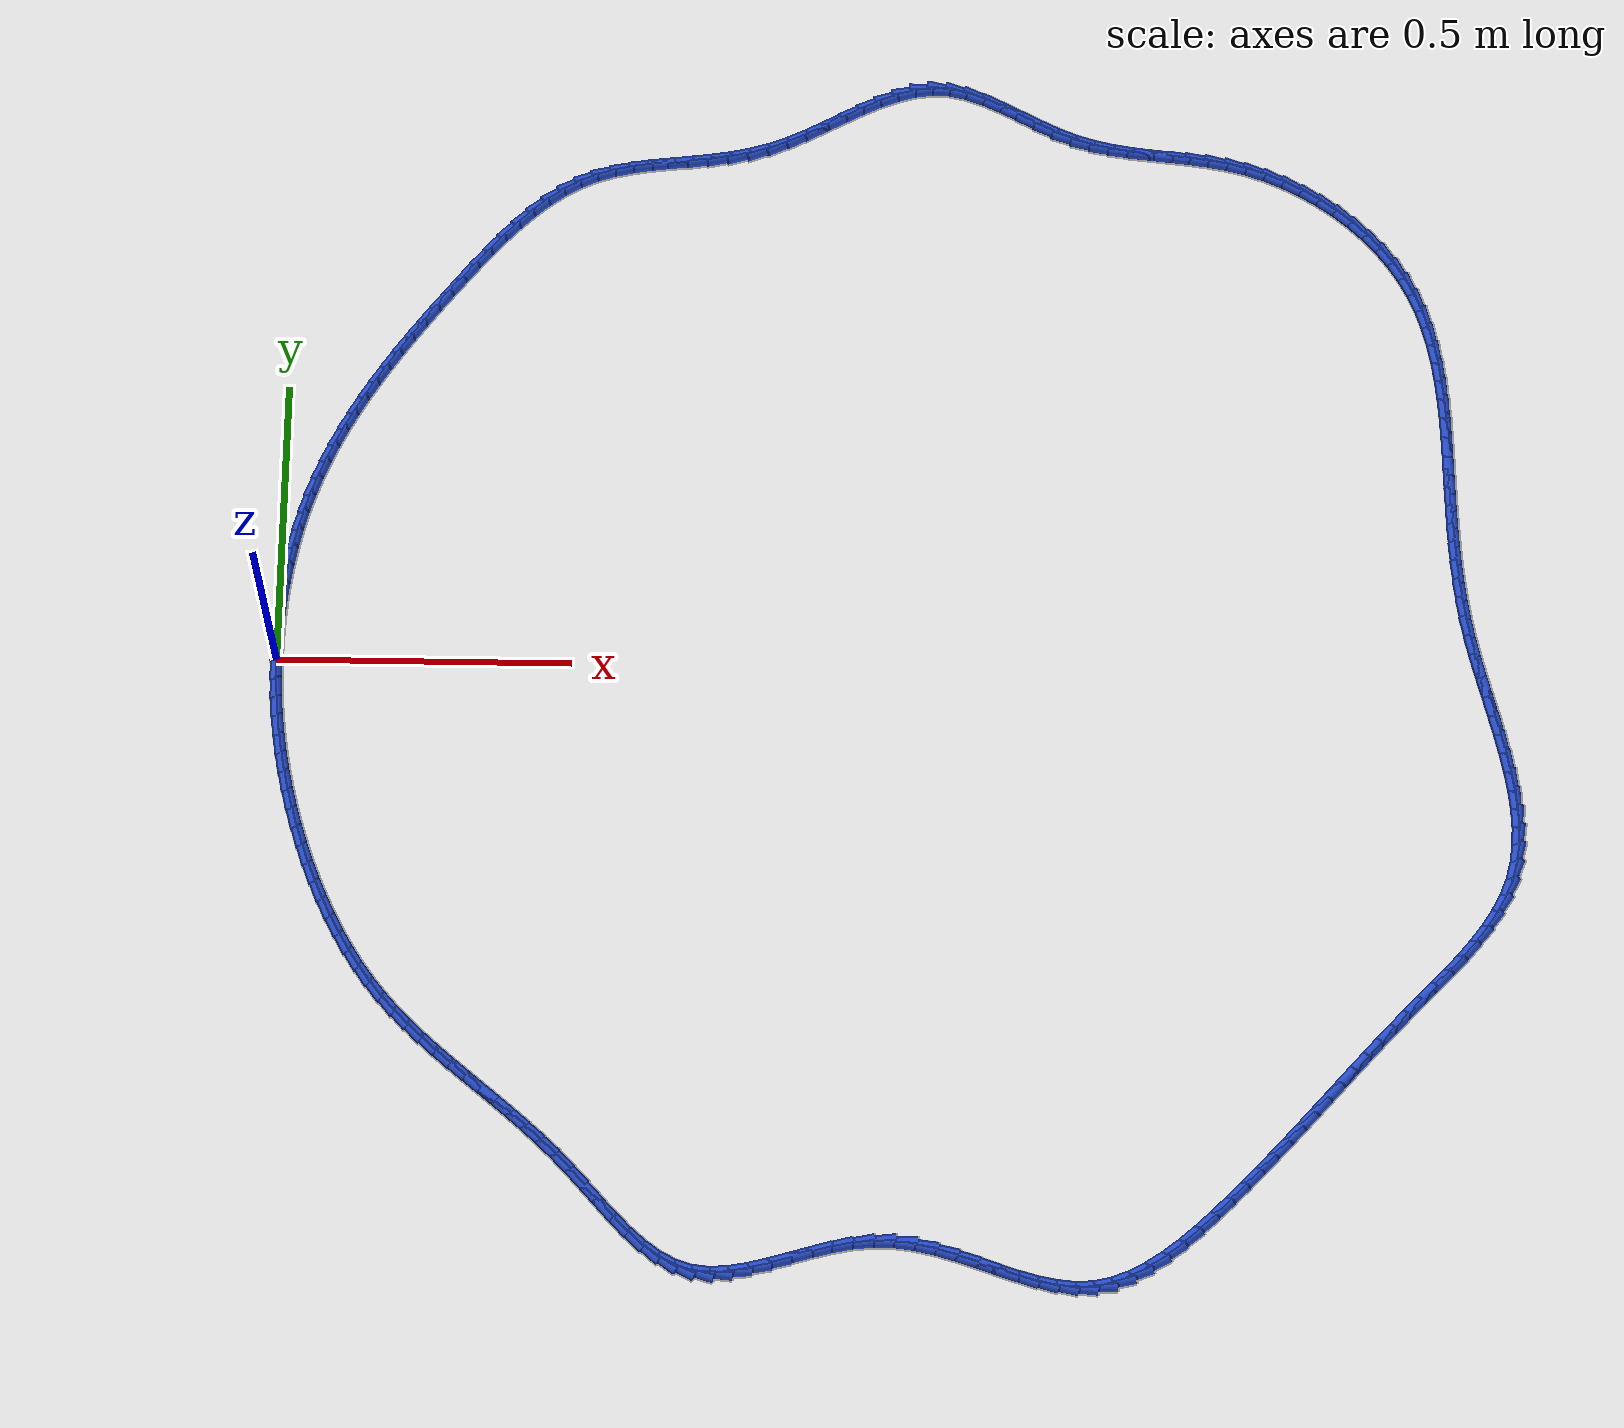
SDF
<sdf version="1.6">
 <world name="default">
  <light name="sun" type="directional">
   <pose>0 0 10 0 -0 0</pose>
   <diffuse>0.8 0.8 0.8 1</diffuse>
   <specular>0.2 0.2 0.2 1</specular>
   <attenuation>
    <range>1000</range>
    <constant>0.9</constant>
    <linear>0.01</linear>
    <quadratic>0.001</quadratic>
   </attenuation>
   <direction>-0.5 0.1 -0.9</direction>
  </light>
  <model name="ground_plane">
   <static>1</static>
   <link name="link">
    <collision name="collision">
     <geometry><plane><normal>0 0 1</normal><size>100 100</size></plane></geometry>
     <surface><friction><ode><mu>100</mu><mu2>50</mu2></ode></friction></surface>
    </collision>
    <visual name="visual">
     <cast_shadows>0</cast_shadows>
     <geometry><plane><normal>0 0 1</normal><size>100 100</size></plane></geometry>
     <material>
      <script><uri>file://media/materials/scripts/gazebo.material</uri><name>Gazebo/WhiteGlow</name></script>
     </material>
    </visual>
   </link>
  </model>
  <gravity>0 0 -9.8</gravity>
  <magnetic_field>6e-06 2.3e-05 -4.2e-05</magnetic_field>
  <atmosphere type="adiabatic"/>
  <physics name="default_physics" default="0" type="ode">
   <max_step_size>0.001</max_step_size>
   <real_time_factor>1</real_time_factor>
   <real_time_update_rate>1000</real_time_update_rate>
  </physics>
  <scene><ambient>0.4 0.4 0.4 1</ambient><background>0.7 0.7 0.7 1</background><shadows>1</shadows></scene>
  <spherical_coordinates>
   <surface_model>EARTH_WGS84</surface_model>
   <latitude_deg>0</latitude_deg>
   <longitude_deg>0</longitude_deg>
   <elevation>0</elevation>
   <heading_deg>0</heading_deg>
  </spherical_coordinates>
  <model name="line">
   <link name="link_0">
    <pose>-2.6020852139652106e-17 -1.3877787807814457e-17 0.01 0 1.57 1.559780961232367</pose>
    <collision name="collision">
     <geometry><cylinder><radius>0.01</radius><length>0.08</length></cylinder></geometry>
    </collision>
    <visual name="visual">
     <material>
      <script><name>Gazebo/Blue</name><uri>file://media/materials/scripts/gazebo.material</uri></script>
     </material>
     <geometry><cylinder><radius>0.01</radius><length>0.08</length></cylinder></geometry>
    </visual>
   </link>
   <link name="link_1">
    <pose>0.00037335531843853863 0.033892676138004445 0.01 0 1.57 1.52627941986492</pose>
    <collision name="collision">
     <geometry><cylinder><radius>0.01</radius><length>0.08</length></cylinder></geometry>
    </collision>
    <visual name="visual">
     <material>
      <script><name>Gazebo/Blue</name><uri>file://media/materials/scripts/gazebo.material</uri></script>
     </material>
     <geometry><cylinder><radius>0.01</radius><length>0.08</length></cylinder></geometry>
    </visual>
   </link>
   <link name="link_2">
    <pose>0.0018848433492593577 0.06782336757025806 0.01 0 1.57 1.4922728739020221</pose>
    <collision name="collision">
     <geometry><cylinder><radius>0.01</radius><length>0.08</length></cylinder></geometry>
    </collision>
    <visual name="visual">
     <material>
      <script><name>Gazebo/Blue</name><uri>file://media/materials/scripts/gazebo.material</uri></script>
     </material>
     <geometry><cylinder><radius>0.01</radius><length>0.08</length></cylinder></geometry>
    </visual>
   </link>
   <link name="link_3">
    <pose>0.004551370837857322 0.10171190142126983 0.01 0 1.57 1.4576042625756793</pose>
    <collision name="collision">
     <geometry><cylinder><radius>0.01</radius><length>0.08</length></cylinder></geometry>
    </collision>
    <visual name="visual">
     <material>
      <script><name>Gazebo/Blue</name><uri>file://media/materials/scripts/gazebo.material</uri></script>
     </material>
     <geometry><cylinder><radius>0.01</radius><length>0.08</length></cylinder></geometry>
    </visual>
   </link>
   <link name="link_4">
    <pose>0.008389844529627322 0.13547810481554898 0.01 0 1.57 1.4221170095015294</pose>
    <collision name="collision">
     <geometry><cylinder><radius>0.01</radius><length>0.08</length></cylinder></geometry>
    </collision>
    <visual name="visual">
     <material>
      <script><name>Gazebo/Blue</name><uri>file://media/materials/scripts/gazebo.material</uri></script>
     </material>
     <geometry><cylinder><radius>0.01</radius><length>0.08</length></cylinder></geometry>
    </visual>
   </link>
   <link name="link_5">
    <pose>0.01341717116996424 0.1690418048776044 0.01 0 1.57 1.3856546378873562</pose>
    <collision name="collision">
     <geometry><cylinder><radius>0.01</radius><length>0.08</length></cylinder></geometry>
    </collision>
    <visual name="visual">
     <material>
      <script><name>Gazebo/Blue</name><uri>file://media/materials/scripts/gazebo.material</uri></script>
     </material>
     <geometry><cylinder><radius>0.01</radius><length>0.08</length></cylinder></geometry>
    </visual>
   </link>
   <link name="link_6">
    <pose>0.019650257504262966 0.20232282873194538 0.01 0 1.57 1.3480608006173773</pose>
    <collision name="collision">
     <geometry><cylinder><radius>0.01</radius><length>0.08</length></cylinder></geometry>
    </collision>
    <visual name="visual">
     <material>
      <script><name>Gazebo/Blue</name><uri>file://media/materials/scripts/gazebo.material</uri></script>
     </material>
     <geometry><cylinder><radius>0.01</radius><length>0.08</length></cylinder></geometry>
    </visual>
   </link>
   <link name="link_7">
    <pose>0.02710601027791841 0.235241003503081 0.01 0 1.57 1.3091798150484968</pose>
    <collision name="collision">
     <geometry><cylinder><radius>0.01</radius><length>0.08</length></cylinder></geometry>
    </collision>
    <visual name="visual">
     <material>
      <script><name>Gazebo/Blue</name><uri>file://media/materials/scripts/gazebo.material</uri></script>
     </material>
     <geometry><cylinder><radius>0.01</radius><length>0.08</length></cylinder></geometry>
    </visual>
   </link>
   <link name="link_8">
    <pose>0.03580133623632542 0.2677161563155202 0.01 0 1.57 1.268857812504629</pose>
    <collision name="collision">
     <geometry><cylinder><radius>0.01</radius><length>0.08</length></cylinder></geometry>
    </collision>
    <visual name="visual">
     <material>
      <script><name>Gazebo/Blue</name><uri>file://media/materials/scripts/gazebo.material</uri></script>
     </material>
     <geometry><cylinder><radius>0.01</radius><length>0.08</length></cylinder></geometry>
    </visual>
   </link>
   <link name="link_9">
    <pose>0.04575314212487891 0.2996681142937721 0.01 0 1.57 1.227158904093968</pose>
    <collision name="collision">
     <geometry><cylinder><radius>0.01</radius><length>0.08</length></cylinder></geometry>
    </collision>
    <visual name="visual">
     <material>
      <script><name>Gazebo/Blue</name><uri>file://media/materials/scripts/gazebo.material</uri></script>
     </material>
     <geometry><cylinder><radius>0.01</radius><length>0.08</length></cylinder></geometry>
    </visual>
   </link>
   <link name="link_10">
    <pose>0.056973408680713884 0.33102411542477467 0.01 0 1.57 1.1862209524761103</pose>
    <collision name="collision">
     <geometry><cylinder><radius>0.01</radius><length>0.08</length></cylinder></geometry>
    </collision>
    <visual name="visual">
     <material>
      <script><name>Gazebo/Blue</name><uri>file://media/materials/scripts/gazebo.material</uri></script>
     </material>
     <geometry><cylinder><radius>0.01</radius><length>0.08</length></cylinder></geometry>
    </visual>
   </link>
   <link name="link_11">
    <pose>0.06942394964834787 0.3617868707075126 0.01 0 1.57 1.147501665228237</pose>
    <collision name="collision">
     <geometry><cylinder><radius>0.01</radius><length>0.08</length></cylinder></geometry>
    </collision>
    <visual name="visual">
     <material>
      <script><name>Gazebo/Blue</name><uri>file://media/materials/scripts/gazebo.material</uri></script>
     </material>
     <geometry><cylinder><radius>0.01</radius><length>0.08</length></cylinder></geometry>
    </visual>
   </link>
   <link name="link_12">
    <pose>0.08303729271888705 0.3920031501237127 0.01 0 1.57 1.1112018715022376</pose>
    <collision name="collision">
     <geometry><cylinder><radius>0.01</radius><length>0.08</length></cylinder></geometry>
    </collision>
    <visual name="visual">
     <material>
      <script><name>Gazebo/Blue</name><uri>file://media/materials/scripts/gazebo.material</uri></script>
     </material>
     <geometry><cylinder><radius>0.01</radius><length>0.08</length></cylinder></geometry>
    </visual>
   </link>
   <link name="link_13">
    <pose>0.09774559889919408 0.4217202753079495 0.01 0 1.57 1.0774592304718202</pose>
    <collision name="collision">
     <geometry><cylinder><radius>0.01</radius><length>0.08</length></cylinder></geometry>
    </collision>
    <visual name="visual">
     <material>
      <script><name>Gazebo/Blue</name><uri>file://media/materials/scripts/gazebo.material</uri></script>
     </material>
     <geometry><cylinder><radius>0.01</radius><length>0.08</length></cylinder></geometry>
    </visual>
   </link>
   <link name="link_14">
    <pose>0.11348102919613148 0.45098556789479716 0.01 0 1.57 1.0463680497749548</pose>
    <collision name="collision">
     <geometry><cylinder><radius>0.01</radius><length>0.08</length></cylinder></geometry>
    </collision>
    <visual name="visual">
     <material>
      <script><name>Gazebo/Blue</name><uri>file://media/materials/scripts/gazebo.material</uri></script>
     </material>
     <geometry><cylinder><radius>0.01</radius><length>0.08</length></cylinder></geometry>
    </visual>
   </link>
   <link name="link_15">
    <pose>0.13017574461656184 0.4798463495188301 0.01 0 1.57 1.0179846152036736</pose>
    <collision name="collision">
     <geometry><cylinder><radius>0.01</radius><length>0.08</length></cylinder></geometry>
    </collision>
    <visual name="visual">
     <material>
      <script><name>Gazebo/Blue</name><uri>file://media/materials/scripts/gazebo.material</uri></script>
     </material>
     <geometry><cylinder><radius>0.01</radius><length>0.08</length></cylinder></geometry>
    </visual>
   </link>
   <link name="link_16">
    <pose>0.14776190616734775 0.5083499418146228 0.01 0 1.57 0.9923332720461119</pose>
    <collision name="collision">
     <geometry><cylinder><radius>0.01</radius><length>0.08</length></cylinder></geometry>
    </collision>
    <visual name="visual">
     <material>
      <script><name>Gazebo/Blue</name><uri>file://media/materials/scripts/gazebo.material</uri></script>
     </material>
     <geometry><cylinder><radius>0.01</radius><length>0.08</length></cylinder></geometry>
    </visual>
   </link>
   <link name="link_17">
    <pose>0.16617167485535186 0.5365436664167496 0.01 0 1.57 0.9694126702443309</pose>
    <collision name="collision">
     <geometry><cylinder><radius>0.01</radius><length>0.08</length></cylinder></geometry>
    </collision>
    <visual name="visual">
     <material>
      <script><name>Gazebo/Blue</name><uri>file://media/materials/scripts/gazebo.material</uri></script>
     </material>
     <geometry><cylinder><radius>0.01</radius><length>0.08</length></cylinder></geometry>
    </visual>
   </link>
   <link name="link_18">
    <pose>0.18533721168743666 0.5644748449597846 0.01 0 1.57 0.9492017358474267</pose>
    <collision name="collision">
     <geometry><cylinder><radius>0.01</radius><length>0.08</length></cylinder></geometry>
    </collision>
    <visual name="visual">
     <material>
      <script><name>Gazebo/Blue</name><uri>file://media/materials/scripts/gazebo.material</uri></script>
     </material>
     <geometry><cylinder><radius>0.01</radius><length>0.08</length></cylinder></geometry>
    </visual>
   </link>
   <link name="link_19">
    <pose>0.20519067767046487 0.5921907990783024 0.01 0 1.57 0.9316650804284664</pose>
    <collision name="collision">
     <geometry><cylinder><radius>0.01</radius><length>0.08</length></cylinder></geometry>
    </collision>
    <visual name="visual">
     <material>
      <script><name>Gazebo/Blue</name><uri>file://media/materials/scripts/gazebo.material</uri></script>
     </material>
     <geometry><cylinder><radius>0.01</radius><length>0.08</length></cylinder></geometry>
    </visual>
   </link>
   <link name="link_20">
    <pose>0.22566423381129905 0.6197388504068774 0.01 0 1.57 0.916757688448729</pose>
    <collision name="collision">
     <geometry><cylinder><radius>0.01</radius><length>0.08</length></cylinder></geometry>
    </collision>
    <visual name="visual">
     <material>
      <script><name>Gazebo/Blue</name><uri>file://media/materials/scripts/gazebo.material</uri></script>
     </material>
     <geometry><cylinder><radius>0.01</radius><length>0.08</length></cylinder></geometry>
    </visual>
   </link>
   <link name="link_21">
    <pose>0.2466900411168016 0.6471663205800836 0.01 0 1.57 0.9044288213493858</pose>
    <collision name="collision">
     <geometry><cylinder><radius>0.01</radius><length>0.08</length></cylinder></geometry>
    </collision>
    <visual name="visual">
     <material>
      <script><name>Gazebo/Blue</name><uri>file://media/materials/scripts/gazebo.material</uri></script>
     </material>
     <geometry><cylinder><radius>0.01</radius><length>0.08</length></cylinder></geometry>
    </visual>
   </link>
   <link name="link_22">
    <pose>0.2682002605938353 0.6745205312324958 0.01 0 1.57 0.8946251457050223</pose>
    <collision name="collision">
     <geometry><cylinder><radius>0.01</radius><length>0.08</length></cylinder></geometry>
    </collision>
    <visual name="visual">
     <material>
      <script><name>Gazebo/Blue</name><uri>file://media/materials/scripts/gazebo.material</uri></script>
     </material>
     <geometry><cylinder><radius>0.01</radius><length>0.08</length></cylinder></geometry>
    </visual>
   </link>
   <link name="link_23">
    <pose>0.29012705324926286 0.7018488039986885 0.01 0 1.57 0.8862440471785034</pose>
    <collision name="collision">
     <geometry><cylinder><radius>0.01</radius><length>0.08</length></cylinder></geometry>
    </collision>
    <visual name="visual">
     <material>
      <script><name>Gazebo/Blue</name><uri>file://media/materials/scripts/gazebo.material</uri></script>
     </material>
     <geometry><cylinder><radius>0.01</radius><length>0.08</length></cylinder></geometry>
    </visual>
   </link>
   <link name="link_24">
    <pose>0.3124186782380927 0.7291596617648045 0.01 0 1.57 0.8712839960348733</pose>
    <collision name="collision">
     <geometry><cylinder><radius>0.01</radius><length>0.08</length></cylinder></geometry>
    </collision>
    <visual name="visual">
     <material>
      <script><name>Gazebo/Blue</name><uri>file://media/materials/scripts/gazebo.material</uri></script>
     </material>
     <geometry><cylinder><radius>0.01</radius><length>0.08</length></cylinder></geometry>
    </visual>
   </link>
   <link name="link_25">
    <pose>0.33514514451881533 0.7561681936658553 0.01 0 1.57 0.8458424188517867</pose>
    <collision name="collision">
     <geometry><cylinder><radius>0.01</radius><length>0.08</length></cylinder></geometry>
    </collision>
    <visual name="visual">
     <material>
      <script><name>Gazebo/Blue</name><uri>file://media/materials/scripts/gazebo.material</uri></script>
     </material>
     <geometry><cylinder><radius>0.01</radius><length>0.08</length></cylinder></geometry>
    </visual>
   </link>
   <link name="link_26">
    <pose>0.3584321345426677 0.7824553080714783 0.01 0 1.57 0.8092626090625994</pose>
    <collision name="collision">
     <geometry><cylinder><radius>0.01</radius><length>0.08</length></cylinder></geometry>
    </collision>
    <visual name="visual">
     <material>
      <script><name>Gazebo/Blue</name><uri>file://media/materials/scripts/gazebo.material</uri></script>
     </material>
     <geometry><cylinder><radius>0.01</radius><length>0.08</length></cylinder></geometry>
    </visual>
   </link>
   <link name="link_27">
    <pose>0.3824056179377343 0.8076012212156577 0.01 0 1.57 0.7605738952245024</pose>
    <collision name="collision">
     <geometry><cylinder><radius>0.01</radius><length>0.08</length></cylinder></geometry>
    </collision>
    <visual name="visual">
     <material>
      <script><name>Gazebo/Blue</name><uri>file://media/materials/scripts/gazebo.material</uri></script>
     </material>
     <geometry><cylinder><radius>0.01</radius><length>0.08</length></cylinder></geometry>
    </visual>
   </link>
   <link name="link_28">
    <pose>0.4071915643321001 0.8311861493323789 0.01 0 1.57 0.6985613777045547</pose>
    <collision name="collision">
     <geometry><cylinder><radius>0.01</radius><length>0.08</length></cylinder></geometry>
    </collision>
    <visual name="visual">
     <material>
      <script><name>Gazebo/Blue</name><uri>file://media/materials/scripts/gazebo.material</uri></script>
     </material>
     <geometry><cylinder><radius>0.01</radius><length>0.08</length></cylinder></geometry>
    </visual>
   </link>
   <link name="link_29">
    <pose>0.43291594335384953 0.8527903086556259 0.01 0 1.57 0.6219470995186506</pose>
    <collision name="collision">
     <geometry><cylinder><radius>0.01</radius><length>0.08</length></cylinder></geometry>
    </collision>
    <visual name="visual">
     <material>
      <script><name>Gazebo/Blue</name><uri>file://media/materials/scripts/gazebo.material</uri></script>
     </material>
     <geometry><cylinder><radius>0.01</radius><length>0.08</length></cylinder></geometry>
    </visual>
   </link>
   <link name="link_30">
    <pose>0.45970472463106754 0.8719939154193841 0.01 0 1.57 0.5297287963512592</pose>
    <collision name="collision">
     <geometry><cylinder><radius>0.01</radius><length>0.08</length></cylinder></geometry>
    </collision>
    <visual name="visual">
     <material>
      <script><name>Gazebo/Blue</name><uri>file://media/materials/scripts/gazebo.material</uri></script>
     </material>
     <geometry><cylinder><radius>0.01</radius><length>0.08</length></cylinder></geometry>
    </visual>
   </link>
   <link name="link_31">
    <pose>0.4876838777918387 0.8883771858576377 0.01 0 1.57 0.42183444499736367</pose>
    <collision name="collision">
     <geometry><cylinder><radius>0.01</radius><length>0.08</length></cylinder></geometry>
    </collision>
    <visual name="visual">
     <material>
      <script><name>Gazebo/Blue</name><uri>file://media/materials/scripts/gazebo.material</uri></script>
     </material>
     <geometry><cylinder><radius>0.01</radius><length>0.08</length></cylinder></geometry>
    </visual>
   </link>
   <link name="link_32">
    <pose>0.5169783435127231 0.9015237990385596 0.01 0 1.57 0.3117104932592036</pose>
    <collision name="collision">
     <geometry><cylinder><radius>0.01</radius><length>0.08</length></cylinder></geometry>
    </collision>
    <visual name="visual">
     <material>
      <script><name>Gazebo/Blue</name><uri>file://media/materials/scripts/gazebo.material</uri></script>
     </material>
     <geometry><cylinder><radius>0.01</radius><length>0.08</length></cylinder></geometry>
    </visual>
   </link>
   <link name="link_33">
    <pose>0.5476020046357374 0.9113911881452095 0.01 0 1.57 0.2243934137685794</pose>
    <collision name="collision">
     <geometry><cylinder><radius>0.01</radius><length>0.08</length></cylinder></geometry>
    </collision>
    <visual name="visual">
     <material>
      <script><name>Gazebo/Blue</name><uri>file://media/materials/scripts/gazebo.material</uri></script>
     </material>
     <geometry><cylinder><radius>0.01</radius><length>0.08</length></cylinder></geometry>
    </visual>
   </link>
   <link name="link_34">
    <pose>0.5793599311999434 0.9186395251153273 0.01 0 1.57 0.16280593449440017</pose>
    <collision name="collision">
     <geometry><cylinder><radius>0.01</radius><length>0.08</length></cylinder></geometry>
    </collision>
    <visual name="visual">
     <material>
      <script><name>Gazebo/Blue</name><uri>file://media/materials/scripts/gazebo.material</uri></script>
     </material>
     <geometry><cylinder><radius>0.01</radius><length>0.08</length></cylinder></geometry>
    </visual>
   </link>
   <link name="link_35">
    <pose>0.6120341348242175 0.9240065827102517 0.01 0 1.57 0.1258885855052466</pose>
    <collision name="collision">
     <geometry><cylinder><radius>0.01</radius><length>0.08</length></cylinder></geometry>
    </collision>
    <visual name="visual">
     <material>
      <script><name>Gazebo/Blue</name><uri>file://media/materials/scripts/gazebo.material</uri></script>
     </material>
     <geometry><cylinder><radius>0.01</radius><length>0.08</length></cylinder></geometry>
    </visual>
   </link>
   <link name="link_36">
    <pose>0.645406627127435 0.9282301336913199 0.01 0 1.57 0.11230251354456235</pose>
    <collision name="collision">
     <geometry><cylinder><radius>0.01</radius><length>0.08</length></cylinder></geometry>
    </collision>
    <visual name="visual">
     <material>
      <script><name>Gazebo/Blue</name><uri>file://media/materials/scripts/gazebo.material</uri></script>
     </material>
     <geometry><cylinder><radius>0.01</radius><length>0.08</length></cylinder></geometry>
    </visual>
   </link>
   <link name="link_37">
    <pose>0.679259419728472 0.9320479508198698 0.01 0 1.57 0.12104806637049734</pose>
    <collision name="collision">
     <geometry><cylinder><radius>0.01</radius><length>0.08</length></cylinder></geometry>
    </collision>
    <visual name="visual">
     <material>
      <script><name>Gazebo/Blue</name><uri>file://media/materials/scripts/gazebo.material</uri></script>
     </material>
     <geometry><cylinder><radius>0.01</radius><length>0.08</length></cylinder></geometry>
    </visual>
   </link>
   <link name="link_38">
    <pose>0.7133745242462044 0.9361978068572392 0.01 0 1.57 0.15163026652183523</pose>
    <collision name="collision">
     <geometry><cylinder><radius>0.01</radius><length>0.08</length></cylinder></geometry>
    </collision>
    <visual name="visual">
     <material>
      <script><name>Gazebo/Blue</name><uri>file://media/materials/scripts/gazebo.material</uri></script>
     </material>
     <geometry><cylinder><radius>0.01</radius><length>0.08</length></cylinder></geometry>
    </visual>
   </link>
   <link name="link_39">
    <pose>0.7475339522995079 0.9414174745647663 0.01 0 1.57 0.20389706775973732</pose>
    <collision name="collision">
     <geometry><cylinder><radius>0.01</radius><length>0.08</length></cylinder></geometry>
    </collision>
    <visual name="visual">
     <material>
      <script><name>Gazebo/Blue</name><uri>file://media/materials/scripts/gazebo.material</uri></script>
     </material>
     <geometry><cylinder><radius>0.01</radius><length>0.08</length></cylinder></geometry>
    </visual>
   </link>
   <link name="link_40">
    <pose>0.7815197155072581 0.9484447267037881 0.01 0 1.57 0.2775920231942689</pose>
    <collision name="collision">
     <geometry><cylinder><radius>0.01</radius><length>0.08</length></cylinder></geometry>
    </collision>
    <visual name="visual">
     <material>
      <script><name>Gazebo/Blue</name><uri>file://media/materials/scripts/gazebo.material</uri></script>
     </material>
     <geometry><cylinder><radius>0.01</radius><length>0.08</length></cylinder></geometry>
    </visual>
   </link>
   <link name="link_41">
    <pose>0.8151138254883312 0.958017336035643 0.01 0 1.57 0.3641641509123342</pose>
    <collision name="collision">
     <geometry><cylinder><radius>0.01</radius><length>0.08</length></cylinder></geometry>
    </collision>
    <visual name="visual">
     <material>
      <script><name>Gazebo/Blue</name><uri>file://media/materials/scripts/gazebo.material</uri></script>
     </material>
     <geometry><cylinder><radius>0.01</radius><length>0.08</length></cylinder></geometry>
    </visual>
   </link>
   <link name="link_42">
    <pose>0.84814307829634 0.9706069135645822 0.01 0 1.57 0.4312037157909366</pose>
    <collision name="collision">
     <geometry><cylinder><radius>0.01</radius><length>0.08</length></cylinder></geometry>
    </collision>
    <visual name="visual">
     <material>
      <script><name>Gazebo/Blue</name><uri>file://media/materials/scripts/gazebo.material</uri></script>
     </material>
     <geometry><cylinder><radius>0.01</radius><length>0.08</length></cylinder></geometry>
    </visual>
   </link>
   <link name="link_43">
    <pose>0.8806250583468191 0.985551181569054 0.01 0 1.57 0.4719431314000235</pose>
    <collision name="collision">
     <geometry><cylinder><radius>0.01</radius><length>0.08</length></cylinder></geometry>
    </collision>
    <visual name="visual">
     <material>
      <script><name>Gazebo/Blue</name><uri>file://media/materials/scripts/gazebo.material</uri></script>
     </material>
     <geometry><cylinder><radius>0.01</radius><length>0.08</length></cylinder></geometry>
    </visual>
   </link>
   <link name="link_44">
    <pose>0.9126281467665751 1.0018859685555745 0.01 0 1.57 0.48778019546282586</pose>
    <collision name="collision">
     <geometry><cylinder><radius>0.01</radius><length>0.08</length></cylinder></geometry>
    </collision>
    <visual name="visual">
     <material>
      <script><name>Gazebo/Blue</name><uri>file://media/materials/scripts/gazebo.material</uri></script>
     </material>
     <geometry><cylinder><radius>0.01</radius><length>0.08</length></cylinder></geometry>
    </visual>
   </link>
   <link name="link_45">
    <pose>0.9442207251242934 1.0186471004045023 0.01 0 1.57 0.47884069125856493</pose>
    <collision name="collision">
     <geometry><cylinder><radius>0.01</radius><length>0.08</length></cylinder></geometry>
    </collision>
    <visual name="visual">
     <material>
      <script><name>Gazebo/Blue</name><uri>file://media/materials/scripts/gazebo.material</uri></script>
     </material>
     <geometry><cylinder><radius>0.01</radius><length>0.08</length></cylinder></geometry>
    </visual>
   </link>
   <link name="link_46">
    <pose>0.9754711749886591 1.0348704029961973 0.01 0 1.57 0.4436423172010366</pose>
    <collision name="collision">
     <geometry><cylinder><radius>0.01</radius><length>0.08</length></cylinder></geometry>
    </collision>
    <visual name="visual">
     <material>
      <script><name>Gazebo/Blue</name><uri>file://media/materials/scripts/gazebo.material</uri></script>
     </material>
     <geometry><cylinder><radius>0.01</radius><length>0.08</length></cylinder></geometry>
    </visual>
   </link>
   <link name="link_47">
    <pose>1.0064478779283572 1.0495917022110182 0.01 0 1.57 0.3790090907359172</pose>
    <collision name="collision">
     <geometry><cylinder><radius>0.01</radius><length>0.08</length></cylinder></geometry>
    </collision>
    <visual name="visual">
     <material>
      <script><name>Gazebo/Blue</name><uri>file://media/materials/scripts/gazebo.material</uri></script>
     </material>
     <geometry><cylinder><radius>0.01</radius><length>0.08</length></cylinder></geometry>
    </visual>
   </link>
   <link name="link_48">
    <pose>1.0372192155120725 1.0618468239293237 0.01 0 1.57 0.2804741701441501</pose>
    <collision name="collision">
     <geometry><cylinder><radius>0.01</radius><length>0.08</length></cylinder></geometry>
    </collision>
    <visual name="visual">
     <material>
      <script><name>Gazebo/Blue</name><uri>file://media/materials/scripts/gazebo.material</uri></script>
     </material>
     <geometry><cylinder><radius>0.01</radius><length>0.08</length></cylinder></geometry>
    </visual>
   </link>
   <link name="link_49">
    <pose>1.0678535693084905 1.0706715940314733 0.01 0 1.57 0.14393907729174926</pose>
    <collision name="collision">
     <geometry><cylinder><radius>0.01</radius><length>0.08</length></cylinder></geometry>
    </collision>
    <visual name="visual">
     <material>
      <script><name>Gazebo/Blue</name><uri>file://media/materials/scripts/gazebo.material</uri></script>
     </material>
     <geometry><cylinder><radius>0.01</radius><length>0.08</length></cylinder></geometry>
    </visual>
   </link>
   <link name="link_50">
    <pose>1.0984193208862962 1.0751018383978261 0.01 0 1.57 -0.029986413830368215</pose>
    <collision name="collision">
     <geometry><cylinder><radius>0.01</radius><length>0.08</length></cylinder></geometry>
    </collision>
    <visual name="visual">
     <material>
      <script><name>Gazebo/Blue</name><uri>file://media/materials/scripts/gazebo.material</uri></script>
     </material>
     <geometry><cylinder><radius>0.01</radius><length>0.08</length></cylinder></geometry>
    </visual>
   </link>
   <link name="link_51">
    <pose>1.1289847688106336 1.0741850154131525 0.01 0 1.57 -0.20641243787156788</pose>
    <collision name="collision">
     <geometry><cylinder><radius>0.01</radius><length>0.08</length></cylinder></geometry>
    </collision>
    <visual name="visual">
     <material>
      <script><name>Gazebo/Blue</name><uri>file://media/materials/scripts/gazebo.material</uri></script>
     </material>
     <geometry><cylinder><radius>0.01</radius><length>0.08</length></cylinder></geometry>
    </visual>
   </link>
   <link name="link_52">
    <pose>1.1596124807842272 1.0677717333208352 0.01 0 1.57 -0.3363719242950403</pose>
    <collision name="collision">
     <geometry><cylinder><radius>0.01</radius><length>0.08</length></cylinder></geometry>
    </collision>
    <visual name="visual">
     <material>
      <script><name>Gazebo/Blue</name><uri>file://media/materials/scripts/gazebo.material</uri></script>
     </material>
     <geometry><cylinder><radius>0.01</radius><length>0.08</length></cylinder></geometry>
    </visual>
   </link>
   <link name="link_53">
    <pose>1.190355680847661 1.0570220648709887 0.01 0 1.57 -0.42003805801263283</pose>
    <collision name="collision">
     <geometry><cylinder><radius>0.01</radius><length>0.08</length></cylinder></geometry>
    </collision>
    <visual name="visual">
     <material>
      <script><name>Gazebo/Blue</name><uri>file://media/materials/scripts/gazebo.material</uri></script>
     </material>
     <geometry><cylinder><radius>0.01</radius><length>0.08</length></cylinder></geometry>
    </visual>
   </link>
   <link name="link_54">
    <pose>1.221266732903337 1.0432166266003546 0.01 0 1.57 -0.4640319095619825</pose>
    <collision name="collision">
     <geometry><cylinder><radius>0.01</radius><length>0.08</length></cylinder></geometry>
    </collision>
    <visual name="visual">
     <material>
      <script><name>Gazebo/Blue</name><uri>file://media/materials/scripts/gazebo.material</uri></script>
     </material>
     <geometry><cylinder><radius>0.01</radius><length>0.08</length></cylinder></geometry>
    </visual>
   </link>
   <link name="link_55">
    <pose>1.2523980008536602 1.0276360350456744 0.01 0 1.57 -0.4731095748066718</pose>
    <collision name="collision">
     <geometry><cylinder><radius>0.01</radius><length>0.08</length></cylinder></geometry>
    </collision>
    <visual name="visual">
     <material>
      <script><name>Gazebo/Blue</name><uri>file://media/materials/scripts/gazebo.material</uri></script>
     </material>
     <geometry><cylinder><radius>0.01</radius><length>0.08</length></cylinder></geometry>
    </visual>
   </link>
   <link name="link_56">
    <pose>1.2838018486010327 1.0115609067436897 0.01 0 1.57 -0.449036031214916</pose>
    <collision name="collision">
     <geometry><cylinder><radius>0.01</radius><length>0.08</length></cylinder></geometry>
    </collision>
    <visual name="visual">
     <material>
      <script><name>Gazebo/Blue</name><uri>file://media/materials/scripts/gazebo.material</uri></script>
     </material>
     <geometry><cylinder><radius>0.01</radius><length>0.08</length></cylinder></geometry>
    </visual>
   </link>
   <link name="link_57">
    <pose>1.3155306400478592 0.9962718582311425 0.01 0 1.57 -0.39066546499401184</pose>
    <collision name="collision">
     <geometry><cylinder><radius>0.01</radius><length>0.08</length></cylinder></geometry>
    </collision>
    <visual name="visual">
     <material>
      <script><name>Gazebo/Blue</name><uri>file://media/materials/scripts/gazebo.material</uri></script>
     </material>
     <geometry><cylinder><radius>0.01</radius><length>0.08</length></cylinder></geometry>
    </visual>
   </link>
   <link name="link_58">
    <pose>1.347636739096542 0.9830495060447745 0.01 0 1.57 -0.3024451211469117</pose>
    <collision name="collision">
     <geometry><cylinder><radius>0.01</radius><length>0.08</length></cylinder></geometry>
    </collision>
    <visual name="visual">
     <material>
      <script><name>Gazebo/Blue</name><uri>file://media/materials/scripts/gazebo.material</uri></script>
     </material>
     <geometry><cylinder><radius>0.01</radius><length>0.08</length></cylinder></geometry>
    </visual>
   </link>
   <link name="link_59">
    <pose>1.3801542135722569 0.9729034890172843 0.01 0 1.57 -0.22098126573274096</pose>
    <collision name="collision">
     <geometry><cylinder><radius>0.01</radius><length>0.08</length></cylinder></geometry>
    </collision>
    <visual name="visual">
     <material>
      <script><name>Gazebo/Blue</name><uri>file://media/materials/scripts/gazebo.material</uri></script>
     </material>
     <geometry><cylinder><radius>0.01</radius><length>0.08</length></cylinder></geometry>
    </visual>
   </link>
   <link name="link_60">
    <pose>1.413027670403558 0.9655184675139443 0.01 0 1.57 -0.15983839966538846</pose>
    <collision name="collision">
     <geometry><cylinder><radius>0.01</radius><length>0.08</length></cylinder></geometry>
    </collision>
    <visual name="visual">
     <material>
      <script><name>Gazebo/Blue</name><uri>file://media/materials/scripts/gazebo.material</uri></script>
     </material>
     <geometry><cylinder><radius>0.01</radius><length>0.08</length></cylinder></geometry>
    </visual>
   </link>
   <link name="link_61">
    <pose>1.4461744158232985 0.9601747594966052 0.01 0 1.57 -0.12007043348917931</pose>
    <collision name="collision">
     <geometry><cylinder><radius>0.01</radius><length>0.08</length></cylinder></geometry>
    </collision>
    <visual name="visual">
     <material>
      <script><name>Gazebo/Blue</name><uri>file://media/materials/scripts/gazebo.material</uri></script>
     </material>
     <geometry><cylinder><radius>0.01</radius><length>0.08</length></cylinder></geometry>
    </visual>
   </link>
   <link name="link_62">
    <pose>1.4795117493639343 0.956152583689529 0.01 0 1.57 -0.10191513880578532</pose>
    <collision name="collision">
     <geometry><cylinder><radius>0.01</radius><length>0.08</length></cylinder></geometry>
    </collision>
    <visual name="visual">
     <material>
      <script><name>Gazebo/Blue</name><uri>file://media/materials/scripts/gazebo.material</uri></script>
     </material>
     <geometry><cylinder><radius>0.01</radius><length>0.08</length></cylinder></geometry>
    </visual>
   </link>
   <link name="link_63">
    <pose>1.5129569705579187 0.9527321588169759 0.01 0 1.57 -0.10532767849726478</pose>
    <collision name="collision">
     <geometry><cylinder><radius>0.01</radius><length>0.08</length></cylinder></geometry>
    </collision>
    <visual name="visual">
     <material>
      <script><name>Gazebo/Blue</name><uri>file://media/materials/scripts/gazebo.material</uri></script>
     </material>
     <geometry><cylinder><radius>0.01</radius><length>0.08</length></cylinder></geometry>
    </visual>
   </link>
   <link name="link_64">
    <pose>1.546427378937707 0.9491937036032077 0.01 0 1.57 -0.13023406003100432</pose>
    <collision name="collision">
     <geometry><cylinder><radius>0.01</radius><length>0.08</length></cylinder></geometry>
    </collision>
    <visual name="visual">
     <material>
      <script><name>Gazebo/Blue</name><uri>file://media/materials/scripts/gazebo.material</uri></script>
     </material>
     <geometry><cylinder><radius>0.01</radius><length>0.08</length></cylinder></geometry>
    </visual>
   </link>
   <link name="link_65">
    <pose>1.5798402740357542 0.9448174367724856 0.01 0 1.57 -0.17648485367301484</pose>
    <collision name="collision">
     <geometry><cylinder><radius>0.01</radius><length>0.08</length></cylinder></geometry>
    </collision>
    <visual name="visual">
     <material>
      <script><name>Gazebo/Blue</name><uri>file://media/materials/scripts/gazebo.material</uri></script>
     </material>
     <geometry><cylinder><radius>0.01</radius><length>0.08</length></cylinder></geometry>
    </visual>
   </link>
   <link name="link_66">
    <pose>1.6131129553845145 0.9388835770490706 0.01 0 1.57 -0.24309536410409505</pose>
    <collision name="collision">
     <geometry><cylinder><radius>0.01</radius><length>0.08</length></cylinder></geometry>
    </collision>
    <visual name="visual">
     <material>
      <script><name>Gazebo/Blue</name><uri>file://media/materials/scripts/gazebo.material</uri></script>
     </material>
     <geometry><cylinder><radius>0.01</radius><length>0.08</length></cylinder></geometry>
    </visual>
   </link>
   <link name="link_67">
    <pose>1.64615996847749 0.9306879199796713 0.01 0 1.57 -0.3183501663747156</pose>
    <collision name="collision">
     <geometry><cylinder><radius>0.01</radius><length>0.08</length></cylinder></geometry>
    </collision>
    <visual name="visual">
     <material>
      <script><name>Gazebo/Blue</name><uri>file://media/materials/scripts/gazebo.material</uri></script>
     </material>
     <geometry><cylinder><radius>0.01</radius><length>0.08</length></cylinder></geometry>
    </visual>
   </link>
   <link name="link_68">
    <pose>1.6788257858484694 0.9199225932146647 0.01 0 1.57 -0.39127411628972586</pose>
    <collision name="collision">
     <geometry><cylinder><radius>0.01</radius><length>0.08</length></cylinder></geometry>
    </collision>
    <visual name="visual">
     <material>
      <script><name>Gazebo/Blue</name><uri>file://media/materials/scripts/gazebo.material</uri></script>
     </material>
     <geometry><cylinder><radius>0.01</radius><length>0.08</length></cylinder></geometry>
    </visual>
   </link>
   <link name="link_69">
    <pose>1.7108808507535485 0.9066984334111637 0.01 0 1.57 -0.4622752365895982</pose>
    <collision name="collision">
     <geometry><cylinder><radius>0.01</radius><length>0.08</length></cylinder></geometry>
    </collision>
    <visual name="visual">
     <material>
      <script><name>Gazebo/Blue</name><uri>file://media/materials/scripts/gazebo.material</uri></script>
     </material>
     <geometry><cylinder><radius>0.01</radius><length>0.08</length></cylinder></geometry>
    </visual>
   </link>
   <link name="link_70">
    <pose>1.7420920603979424 0.8911463336619099 0.01 0 1.57 -0.532293784953534</pose>
    <collision name="collision">
     <geometry><cylinder><radius>0.01</radius><length>0.08</length></cylinder></geometry>
    </collision>
    <visual name="visual">
     <material>
      <script><name>Gazebo/Blue</name><uri>file://media/materials/scripts/gazebo.material</uri></script>
     </material>
     <geometry><cylinder><radius>0.01</radius><length>0.08</length></cylinder></geometry>
    </visual>
   </link>
   <link name="link_71">
    <pose>1.7722263119868658 0.8733971870596442 0.01 0 1.57 -0.60225599495063</pose>
    <collision name="collision">
     <geometry><cylinder><radius>0.01</radius><length>0.08</length></cylinder></geometry>
    </collision>
    <visual name="visual">
     <material>
      <script><name>Gazebo/Blue</name><uri>file://media/materials/scripts/gazebo.material</uri></script>
     </material>
     <geometry><cylinder><radius>0.01</radius><length>0.08</length></cylinder></geometry>
    </visual>
   </link>
   <link name="link_72">
    <pose>1.8010505027255335 0.8535818866971076 0.01 0 1.57 -0.6730789430408101</pose>
    <collision name="collision">
     <geometry><cylinder><radius>0.01</radius><length>0.08</length></cylinder></geometry>
    </collision>
    <visual name="visual">
     <material>
      <script><name>Gazebo/Blue</name><uri>file://media/materials/scripts/gazebo.material</uri></script>
     </material>
     <geometry><cylinder><radius>0.01</radius><length>0.08</length></cylinder></geometry>
    </visual>
   </link>
   <link name="link_73">
    <pose>1.8283315298191591 0.8318313256670412 0.01 0 1.57 -0.7456749934348822</pose>
    <collision name="collision">
     <geometry><cylinder><radius>0.01</radius><length>0.08</length></cylinder></geometry>
    </collision>
    <visual name="visual">
     <material>
      <script><name>Gazebo/Blue</name><uri>file://media/materials/scripts/gazebo.material</uri></script>
     </material>
     <geometry><cylinder><radius>0.01</radius><length>0.08</length></cylinder></geometry>
    </visual>
   </link>
   <link name="link_74">
    <pose>1.8538362904729593 0.8082763970621867 0.01 0 1.57 -0.8209512527114518</pose>
    <collision name="collision">
     <geometry><cylinder><radius>0.01</radius><length>0.08</length></cylinder></geometry>
    </collision>
    <visual name="visual">
     <material>
      <script><name>Gazebo/Blue</name><uri>file://media/materials/scripts/gazebo.material</uri></script>
     </material>
     <geometry><cylinder><radius>0.01</radius><length>0.08</length></cylinder></geometry>
    </visual>
   </link>
   <link name="link_75">
    <pose>1.8773316818921466 0.7830479939752845 0.01 0 1.57 -0.899798930314027</pose>
    <collision name="collision">
     <geometry><cylinder><radius>0.01</radius><length>0.08</length></cylinder></geometry>
    </collision>
    <visual name="visual">
     <material>
      <script><name>Gazebo/Blue</name><uri>file://media/materials/scripts/gazebo.material</uri></script>
     </material>
     <geometry><cylinder><radius>0.01</radius><length>0.08</length></cylinder></geometry>
    </visual>
   </link>
   <link name="link_76">
    <pose>1.8985846012819376 0.7562770094990765 0.01 0 1.57 -0.9830665415049503</pose>
    <collision name="collision">
     <geometry><cylinder><radius>0.01</radius><length>0.08</length></cylinder></geometry>
    </collision>
    <visual name="visual">
     <material>
      <script><name>Gazebo/Blue</name><uri>file://media/materials/scripts/gazebo.material</uri></script>
     </material>
     <geometry><cylinder><radius>0.01</radius><length>0.08</length></cylinder></geometry>
    </visual>
   </link>
   <link name="link_77">
    <pose>1.917361945847545 0.7280943367263035 0.01 0 1.57 -1.0709971660193685</pose>
    <collision name="collision">
     <geometry><cylinder><radius>0.01</radius><length>0.08</length></cylinder></geometry>
    </collision>
    <visual name="visual">
     <material>
      <script><name>Gazebo/Blue</name><uri>file://media/materials/scripts/gazebo.material</uri></script>
     </material>
     <geometry><cylinder><radius>0.01</radius><length>0.08</length></cylinder></geometry>
    </visual>
   </link>
   <link name="link_78">
    <pose>1.9334497990003798 0.6986316565140339 0.01 0 1.57 -1.1564975452425064</pose>
    <collision name="collision">
     <geometry><cylinder><radius>0.01</radius><length>0.08</length></cylinder></geometry>
    </collision>
    <visual name="visual">
     <material>
      <script><name>Gazebo/Blue</name><uri>file://media/materials/scripts/gazebo.material</uri></script>
     </material>
     <geometry><cylinder><radius>0.01</radius><length>0.08</length></cylinder></geometry>
    </visual>
   </link>
   <link name="link_79">
    <pose>1.9469061304280308 0.6680318130680081 0.01 0 1.57 -1.233289392907944</pose>
    <collision name="collision">
     <geometry><cylinder><radius>0.01</radius><length>0.08</length></cylinder></geometry>
    </collision>
    <visual name="visual">
     <material>
      <script><name>Gazebo/Blue</name><uri>file://media/materials/scripts/gazebo.material</uri></script>
     </material>
     <geometry><cylinder><radius>0.01</radius><length>0.08</length></cylinder></geometry>
    </visual>
   </link>
   <link name="link_80">
    <pose>1.9579906988065894 0.6364459358258229 0.01 0 1.57 -1.3006623043660834</pose>
    <collision name="collision">
     <geometry><cylinder><radius>0.01</radius><length>0.08</length></cylinder></geometry>
    </collision>
    <visual name="visual">
     <material>
      <script><name>Gazebo/Blue</name><uri>file://media/materials/scripts/gazebo.material</uri></script>
     </material>
     <geometry><cylinder><radius>0.01</radius><length>0.08</length></cylinder></geometry>
    </visual>
   </link>
   <link name="link_81">
    <pose>1.9669680376984513 0.604025350276606 0.01 0 1.57 -1.3585210095250324</pose>
    <collision name="collision">
     <geometry><cylinder><radius>0.01</radius><length>0.08</length></cylinder></geometry>
    </collision>
    <visual name="visual">
     <material>
      <script><name>Gazebo/Blue</name><uri>file://media/materials/scripts/gazebo.material</uri></script>
     </material>
     <geometry><cylinder><radius>0.01</radius><length>0.08</length></cylinder></geometry>
    </visual>
   </link>
   <link name="link_82">
    <pose>1.9741026806660118 0.570921381909485 0.01 0 1.57 -1.4070805378561995</pose>
    <collision name="collision">
     <geometry><cylinder><radius>0.01</radius><length>0.08</length></cylinder></geometry>
    </collision>
    <visual name="visual">
     <material>
      <script><name>Gazebo/Blue</name><uri>file://media/materials/scripts/gazebo.material</uri></script>
     </material>
     <geometry><cylinder><radius>0.01</radius><length>0.08</length></cylinder></geometry>
    </visual>
   </link>
   <link name="link_83">
    <pose>1.9796591612716676 0.5372853562135881 0.01 0 1.57 -1.446708876610084</pose>
    <collision name="collision">
     <geometry><cylinder><radius>0.01</radius><length>0.08</length></cylinder></geometry>
    </collision>
    <visual name="visual">
     <material>
      <script><name>Gazebo/Blue</name><uri>file://media/materials/scripts/gazebo.material</uri></script>
     </material>
     <geometry><cylinder><radius>0.01</radius><length>0.08</length></cylinder></geometry>
    </visual>
   </link>
   <link name="link_84">
    <pose>1.9839020130778149 0.5032685986780432 0.01 0 1.57 -1.477806476081648</pose>
    <collision name="collision">
     <geometry><cylinder><radius>0.01</radius><length>0.08</length></cylinder></geometry>
    </collision>
    <visual name="visual">
     <material>
      <script><name>Gazebo/Blue</name><uri>file://media/materials/scripts/gazebo.material</uri></script>
     </material>
     <geometry><cylinder><radius>0.01</radius><length>0.08</length></cylinder></geometry>
    </visual>
   </link>
   <link name="link_85">
    <pose>1.9870957696468492 0.46902243479197714 0.01 0 1.57 -1.5007219454036858</pose>
    <collision name="collision">
     <geometry><cylinder><radius>0.01</radius><length>0.08</length></cylinder></geometry>
    </collision>
    <visual name="visual">
     <material>
      <script><name>Gazebo/Blue</name><uri>file://media/materials/scripts/gazebo.material</uri></script>
     </material>
     <geometry><cylinder><radius>0.01</radius><length>0.08</length></cylinder></geometry>
    </visual>
   </link>
   <link name="link_86">
    <pose>1.9895049645411664 0.43469819004451843 0.01 0 1.57 -1.5156956145295342</pose>
    <collision name="collision">
     <geometry><cylinder><radius>0.01</radius><length>0.08</length></cylinder></geometry>
    </collision>
    <visual name="visual">
     <material>
      <script><name>Gazebo/Blue</name><uri>file://media/materials/scripts/gazebo.material</uri></script>
     </material>
     <geometry><cylinder><radius>0.01</radius><length>0.08</length></cylinder></geometry>
    </visual>
   </link>
   <link name="link_87">
    <pose>1.9913941313231633 0.4004471899247946 0.01 0 1.57 -1.5228408383075995</pose>
    <collision name="collision">
     <geometry><cylinder><radius>0.01</radius><length>0.08</length></cylinder></geometry>
    </collision>
    <visual name="visual">
     <material>
      <script><name>Gazebo/Blue</name><uri>file://media/materials/scripts/gazebo.material</uri></script>
     </material>
     <geometry><cylinder><radius>0.01</radius><length>0.08</length></cylinder></geometry>
    </visual>
   </link>
   <link name="link_88">
    <pose>1.9930271979392864 0.36641949871628443 0.01 0 1.57 -1.5233449836789814</pose>
    <collision name="collision">
     <geometry><cylinder><radius>0.01</radius><length>0.08</length></cylinder></geometry>
    </collision>
    <visual name="visual">
     <material>
      <script><name>Gazebo/Blue</name><uri>file://media/materials/scripts/gazebo.material</uri></script>
     </material>
     <geometry><cylinder><radius>0.01</radius><length>0.08</length></cylinder></geometry>
    </visual>
   </link>
   <link name="link_89">
    <pose>1.9946291875739375 0.3326841608651299 0.01 0 1.57 -1.5190822033623217</pose>
    <collision name="collision">
     <geometry><cylinder><radius>0.01</radius><length>0.08</length></cylinder></geometry>
    </collision>
    <visual name="visual">
     <material>
      <script><name>Gazebo/Blue</name><uri>file://media/materials/scripts/gazebo.material</uri></script>
     </material>
     <geometry><cylinder><radius>0.01</radius><length>0.08</length></cylinder></geometry>
    </visual>
   </link>
   <link name="link_90">
    <pose>1.996363296283015 0.29918146475699925 0.01 0 1.57 -1.510167396439507</pose>
    <collision name="collision">
     <geometry><cylinder><radius>0.01</radius><length>0.08</length></cylinder></geometry>
    </collision>
    <visual name="visual">
     <material>
      <script><name>Gazebo/Blue</name><uri>file://media/materials/scripts/gazebo.material</uri></script>
     </material>
     <geometry><cylinder><radius>0.01</radius><length>0.08</length></cylinder></geometry>
    </visual>
   </link>
   <link name="link_91">
    <pose>1.9983872193712962 0.26584024336857126 0.01 0 1.57 -1.496605984101501</pose>
    <collision name="collision">
     <geometry><cylinder><radius>0.01</radius><length>0.08</length></cylinder></geometry>
    </collision>
    <visual name="visual">
     <material>
      <script><name>Gazebo/Blue</name><uri>file://media/materials/scripts/gazebo.material</uri></script>
     </material>
     <geometry><cylinder><radius>0.01</radius><length>0.08</length></cylinder></geometry>
    </visual>
   </link>
   <link name="link_92">
    <pose>2.000858652143558 0.23258932967652476 0.01 0 1.57 -1.478478277776199</pose>
    <collision name="collision">
     <geometry><cylinder><radius>0.01</radius><length>0.08</length></cylinder></geometry>
    </collision>
    <visual name="visual">
     <material>
      <script><name>Gazebo/Blue</name><uri>file://media/materials/scripts/gazebo.material</uri></script>
     </material>
     <geometry><cylinder><radius>0.01</radius><length>0.08</length></cylinder></geometry>
    </visual>
   </link>
   <link name="link_93">
    <pose>2.00393528990458 0.19935755665753882 0.01 0 1.57 -1.4559464162789537</pose>
    <collision name="collision">
     <geometry><cylinder><radius>0.01</radius><length>0.08</length></cylinder></geometry>
    </collision>
    <visual name="visual">
     <material>
      <script><name>Gazebo/Blue</name><uri>file://media/materials/scripts/gazebo.material</uri></script>
     </material>
     <geometry><cylinder><radius>0.01</radius><length>0.08</length></cylinder></geometry>
    </visual>
   </link>
   <link name="link_94">
    <pose>2.00777482795914 0.16607375728829202 0.01 0 1.57 -1.4292599339389893</pose>
    <collision name="collision">
     <geometry><cylinder><radius>0.01</radius><length>0.08</length></cylinder></geometry>
    </collision>
    <visual name="visual">
     <material>
      <script><name>Gazebo/Blue</name><uri>file://media/materials/scripts/gazebo.material</uri></script>
     </material>
     <geometry><cylinder><radius>0.01</radius><length>0.08</length></cylinder></geometry>
    </visual>
   </link>
   <link name="link_95">
    <pose>2.012534961612015 0.13266676454546353 0.01 0 1.57 -1.3987583006290591</pose>
    <collision name="collision">
     <geometry><cylinder><radius>0.01</radius><length>0.08</length></cylinder></geometry>
    </collision>
    <visual name="visual">
     <material>
      <script><name>Gazebo/Blue</name><uri>file://media/materials/scripts/gazebo.material</uri></script>
     </material>
     <geometry><cylinder><radius>0.01</radius><length>0.08</length></cylinder></geometry>
    </visual>
   </link>
   <link name="link_96">
    <pose>2.018373386167985 0.09906541140573244 0.01 0 1.57 -1.3648761212926634</pose>
    <collision name="collision">
     <geometry><cylinder><radius>0.01</radius><length>0.08</length></cylinder></geometry>
    </collision>
    <visual name="visual">
     <material>
      <script><name>Gazebo/Blue</name><uri>file://media/materials/scripts/gazebo.material</uri></script>
     </material>
     <geometry><cylinder><radius>0.01</radius><length>0.08</length></cylinder></geometry>
    </visual>
   </link>
   <link name="link_97">
    <pose>2.0254475161779903 0.06519861445266802 0.01 0 1.57 -1.331668918243753</pose>
    <collision name="collision">
     <geometry><cylinder><radius>0.01</radius><length>0.08</length></cylinder></geometry>
    </collision>
    <visual name="visual">
     <material>
      <script><name>Gazebo/Blue</name><uri>file://media/materials/scripts/gazebo.material</uri></script>
     </material>
     <geometry><cylinder><radius>0.01</radius><length>0.08</length></cylinder></geometry>
    </visual>
   </link>
   <link name="link_98">
    <pose>2.033775935696008 0.03103663320011315 0.01 0 1.57 -1.3082714882466349</pose>
    <collision name="collision">
     <geometry><cylinder><radius>0.01</radius><length>0.08</length></cylinder></geometry>
    </collision>
    <visual name="visual">
     <material>
      <script><name>Gazebo/Blue</name><uri>file://media/materials/scripts/gazebo.material</uri></script>
     </material>
     <geometry><cylinder><radius>0.01</radius><length>0.08</length></cylinder></geometry>
    </visual>
   </link>
   <link name="link_99">
    <pose>2.043014463964983 -0.0033422435461452 0.01 0 1.57 -1.2954796317982198</pose>
    <collision name="collision">
     <geometry><cylinder><radius>0.01</radius><length>0.08</length></cylinder></geometry>
    </collision>
    <visual name="visual">
     <material>
      <script><name>Gazebo/Blue</name><uri>file://media/materials/scripts/gazebo.material</uri></script>
     </material>
     <geometry><cylinder><radius>0.01</radius><length>0.08</length></cylinder></geometry>
    </visual>
   </link>
   <link name="link_100">
    <pose>2.052760404331636 -0.03784230128012907 0.01 0 1.57 -1.2928657004499193</pose>
    <collision name="collision">
     <geometry><cylinder><radius>0.01</radius><length>0.08</length></cylinder></geometry>
    </collision>
    <visual name="visual">
     <material>
      <script><name>Gazebo/Blue</name><uri>file://media/materials/scripts/gazebo.material</uri></script>
     </material>
     <geometry><cylinder><radius>0.01</radius><length>0.08</length></cylinder></geometry>
    </visual>
   </link>
   <link name="link_101">
    <pose>2.0626110601426846 -0.07236782549586042 0.01 0 1.57 -1.300340881489207</pose>
    <collision name="collision">
     <geometry><cylinder><radius>0.01</radius><length>0.08</length></cylinder></geometry>
    </collision>
    <visual name="visual">
     <material>
      <script><name>Gazebo/Blue</name><uri>file://media/materials/scripts/gazebo.material</uri></script>
     </material>
     <geometry><cylinder><radius>0.01</radius><length>0.08</length></cylinder></geometry>
    </visual>
   </link>
   <link name="link_102">
    <pose>2.072163734744849 -0.10682310168736132 0.01 0 1.57 -1.3181561531831159</pose>
    <collision name="collision">
     <geometry><cylinder><radius>0.01</radius><length>0.08</length></cylinder></geometry>
    </collision>
    <visual name="visual">
     <material>
      <script><name>Gazebo/Blue</name><uri>file://media/materials/scripts/gazebo.material</uri></script>
     </material>
     <geometry><cylinder><radius>0.01</radius><length>0.08</length></cylinder></geometry>
    </visual>
   </link>
   <link name="link_103">
    <pose>2.081015731484849 -0.14111241534865382 0.01 0 1.57 -1.3468986863136536</pose>
    <collision name="collision">
     <geometry><cylinder><radius>0.01</radius><length>0.08</length></cylinder></geometry>
    </collision>
    <visual name="visual">
     <material>
      <script><name>Gazebo/Blue</name><uri>file://media/materials/scripts/gazebo.material</uri></script>
     </material>
     <geometry><cylinder><radius>0.01</radius><length>0.08</length></cylinder></geometry>
    </visual>
   </link>
   <link name="link_104">
    <pose>2.0887643537094034 -0.1751400519737599 0.01 0 1.57 -1.38747530946897</pose>
    <collision name="collision">
     <geometry><cylinder><radius>0.01</radius><length>0.08</length></cylinder></geometry>
    </collision>
    <visual name="visual">
     <material>
      <script><name>Gazebo/Blue</name><uri>file://media/materials/scripts/gazebo.material</uri></script>
     </material>
     <geometry><cylinder><radius>0.01</radius><length>0.08</length></cylinder></geometry>
    </visual>
   </link>
   <link name="link_105">
    <pose>2.095006904765232 -0.20881029705670157 0.01 0 1.57 -1.441060845726249</pose>
    <collision name="collision">
     <geometry><cylinder><radius>0.01</radius><length>0.08</length></cylinder></geometry>
    </collision>
    <visual name="visual">
     <material>
      <script><name>Gazebo/Blue</name><uri>file://media/materials/scripts/gazebo.material</uri></script>
     </material>
     <geometry><cylinder><radius>0.01</radius><length>0.08</length></cylinder></geometry>
    </visual>
   </link>
   <link name="link_106">
    <pose>2.099340687999055 -0.24202743609150087 0.01 0 1.57 -1.5089706350856322</pose>
    <collision name="collision">
     <geometry><cylinder><radius>0.01</radius><length>0.08</length></cylinder></geometry>
    </collision>
    <visual name="visual">
     <material>
      <script><name>Gazebo/Blue</name><uri>file://media/materials/scripts/gazebo.material</uri></script>
     </material>
     <geometry><cylinder><radius>0.01</radius><length>0.08</length></cylinder></geometry>
    </visual>
   </link>
   <link name="link_107">
    <pose>2.10136300675759 -0.2746957545721799 0.01 0 1.57 1.5491956696917462</pose>
    <collision name="collision">
     <geometry><cylinder><radius>0.01</radius><length>0.08</length></cylinder></geometry>
    </collision>
    <visual name="visual">
     <material>
      <script><name>Gazebo/Blue</name><uri>file://media/materials/scripts/gazebo.material</uri></script>
     </material>
     <geometry><cylinder><radius>0.01</radius><length>0.08</length></cylinder></geometry>
    </visual>
   </link>
   <link name="link_108">
    <pose>2.1006711643875575 -0.30671953799276047 0.01 0 1.57 1.44964480972993</pose>
    <collision name="collision">
     <geometry><cylinder><radius>0.01</radius><length>0.08</length></cylinder></geometry>
    </collision>
    <visual name="visual">
     <material>
      <script><name>Gazebo/Blue</name><uri>file://media/materials/scripts/gazebo.material</uri></script>
     </material>
     <geometry><cylinder><radius>0.01</radius><length>0.08</length></cylinder></geometry>
    </visual>
   </link>
   <link name="link_109">
    <pose>2.096862464235678 -0.3380030718472649 0.01 0 1.57 1.3346043359116968</pose>
    <collision name="collision">
     <geometry><cylinder><radius>0.01</radius><length>0.08</length></cylinder></geometry>
    </collision>
    <visual name="visual">
     <material>
      <script><name>Gazebo/Blue</name><uri>file://media/materials/scripts/gazebo.material</uri></script>
     </material>
     <geometry><cylinder><radius>0.01</radius><length>0.08</length></cylinder></geometry>
    </visual>
   </link>
   <link name="link_110">
    <pose>2.089534209648669 -0.36845064162971497 0.01 0 1.57 1.209423610528037</pose>
    <collision name="collision">
     <geometry><cylinder><radius>0.01</radius><length>0.08</length></cylinder></geometry>
    </collision>
    <visual name="visual">
     <material>
      <script><name>Gazebo/Blue</name><uri>file://media/materials/scripts/gazebo.material</uri></script>
     </material>
     <geometry><cylinder><radius>0.01</radius><length>0.08</length></cylinder></geometry>
    </visual>
   </link>
   <link name="link_111">
    <pose>2.0783714708034644 -0.3979839731634288 0.01 0 1.57 1.096923491500316</pose>
    <collision name="collision">
     <geometry><cylinder><radius>0.01</radius><length>0.08</length></cylinder></geometry>
    </collision>
    <visual name="visual">
     <material>
      <script><name>Gazebo/Blue</name><uri>file://media/materials/scripts/gazebo.material</uri></script>
     </material>
     <geometry><cylinder><radius>0.01</radius><length>0.08</length></cylinder></geometry>
    </visual>
   </link>
   <link name="link_112">
    <pose>2.0636719460082817 -0.4266465288813257 0.01 0 1.57 1.0058258915136158</pose>
    <collision name="collision">
     <geometry><cylinder><radius>0.01</radius><length>0.08</length></cylinder></geometry>
    </collision>
    <visual name="visual">
     <material>
      <script><name>Gazebo/Blue</name><uri>file://media/materials/scripts/gazebo.material</uri></script>
     </material>
     <geometry><cylinder><radius>0.01</radius><length>0.08</length></cylinder></geometry>
    </visual>
   </link>
   <link name="link_113">
    <pose>2.045994426526122 -0.4545336535401736 0.01 0 1.57 0.9346194919334821</pose>
    <collision name="collision">
     <geometry><cylinder><radius>0.01</radius><length>0.08</length></cylinder></geometry>
    </collision>
    <visual name="visual">
     <material>
      <script><name>Gazebo/Blue</name><uri>file://media/materials/scripts/gazebo.material</uri></script>
     </material>
     <geometry><cylinder><radius>0.01</radius><length>0.08</length></cylinder></geometry>
    </visual>
   </link>
   <link name="link_114">
    <pose>2.025898672254944 -0.48174088437620666 0.01 0 1.57 0.8812118195374132</pose>
    <collision name="collision">
     <geometry><cylinder><radius>0.01</radius><length>0.08</length></cylinder></geometry>
    </collision>
    <visual name="visual">
     <material>
      <script><name>Gazebo/Blue</name><uri>file://media/materials/scripts/gazebo.material</uri></script>
     </material>
     <geometry><cylinder><radius>0.01</radius><length>0.08</length></cylinder></geometry>
    </visual>
   </link>
   <link name="link_115">
    <pose>2.003944443092711 -0.5083637586256596 0.01 0 1.57 0.843669552036305</pose>
    <collision name="collision">
     <geometry><cylinder><radius>0.01</radius><length>0.08</length></cylinder></geometry>
    </collision>
    <visual name="visual">
     <material>
      <script><name>Gazebo/Blue</name><uri>file://media/materials/scripts/gazebo.material</uri></script>
     </material>
     <geometry><cylinder><radius>0.01</radius><length>0.08</length></cylinder></geometry>
    </visual>
   </link>
   <link name="link_116">
    <pose>1.9806914989373838 -0.5344978135247664 0.01 0 1.57 0.8205491638386662</pose>
    <collision name="collision">
     <geometry><cylinder><radius>0.01</radius><length>0.08</length></cylinder></geometry>
    </collision>
    <visual name="visual">
     <material>
      <script><name>Gazebo/Blue</name><uri>file://media/materials/scripts/gazebo.material</uri></script>
     </material>
     <geometry><cylinder><radius>0.01</radius><length>0.08</length></cylinder></geometry>
    </visual>
   </link>
   <link name="link_117">
    <pose>1.9566995996869232 -0.5602385863097629 0.01 0 1.57 0.8110290696298452</pose>
    <collision name="collision">
     <geometry><cylinder><radius>0.01</radius><length>0.08</length></cylinder></geometry>
    </collision>
    <visual name="visual">
     <material>
      <script><name>Gazebo/Blue</name><uri>file://media/materials/scripts/gazebo.material</uri></script>
     </material>
     <geometry><cylinder><radius>0.01</radius><length>0.08</length></cylinder></geometry>
    </visual>
   </link>
   <link name="link_118">
    <pose>1.9325285052392909 -0.5856816142168829 0.01 0 1.57 0.8147751303347857</pose>
    <collision name="collision">
     <geometry><cylinder><radius>0.01</radius><length>0.08</length></cylinder></geometry>
    </collision>
    <visual name="visual">
     <material>
      <script><name>Gazebo/Blue</name><uri>file://media/materials/scripts/gazebo.material</uri></script>
     </material>
     <geometry><cylinder><radius>0.01</radius><length>0.08</length></cylinder></geometry>
    </visual>
   </link>
   <link name="link_119">
    <pose>1.9087295957915758 -0.6109215507849404 0.01 0 1.57 0.8254772274303617</pose>
    <collision name="collision">
     <geometry><cylinder><radius>0.01</radius><length>0.08</length></cylinder></geometry>
    </collision>
    <visual name="visual">
     <material>
      <script><name>Gazebo/Blue</name><uri>file://media/materials/scripts/gazebo.material</uri></script>
     </material>
     <geometry><cylinder><radius>0.01</radius><length>0.08</length></cylinder></geometry>
    </visual>
   </link>
   <link name="link_120">
    <pose>1.8855641910838412 -0.6360224606711479 0.01 0 1.57 0.8349274374636908</pose>
    <collision name="collision">
     <geometry><cylinder><radius>0.01</radius><length>0.08</length></cylinder></geometry>
    </collision>
    <visual name="visual">
     <material>
      <script><name>Gazebo/Blue</name><uri>file://media/materials/scripts/gazebo.material</uri></script>
     </material>
     <geometry><cylinder><radius>0.01</radius><length>0.08</length></cylinder></geometry>
    </visual>
   </link>
   <link name="link_121">
    <pose>1.8629362549979693 -0.6610107228855716 0.01 0 1.57 0.8424630305905666</pose>
    <collision name="collision">
     <geometry><cylinder><radius>0.01</radius><length>0.08</length></cylinder></geometry>
    </collision>
    <visual name="visual">
     <material>
      <script><name>Gazebo/Blue</name><uri>file://media/materials/scripts/gazebo.material</uri></script>
     </material>
     <geometry><cylinder><radius>0.01</radius><length>0.08</length></cylinder></geometry>
    </visual>
   </link>
   <link name="link_122">
    <pose>1.8407277287025947 -0.6859103939908286 0.01 0 1.57 0.8479569134185778</pose>
    <collision name="collision">
     <geometry><cylinder><radius>0.01</radius><length>0.08</length></cylinder></geometry>
    </collision>
    <visual name="visual">
     <material>
      <script><name>Gazebo/Blue</name><uri>file://media/materials/scripts/gazebo.material</uri></script>
     </material>
     <geometry><cylinder><radius>0.01</radius><length>0.08</length></cylinder></geometry>
    </visual>
   </link>
   <link name="link_123">
    <pose>1.818820553366352 -0.7107455305495374 0.01 0 1.57 0.8513143874718408</pose>
    <collision name="collision">
     <geometry><cylinder><radius>0.01</radius><length>0.08</length></cylinder></geometry>
    </collision>
    <visual name="visual">
     <material>
      <script><name>Gazebo/Blue</name><uri>file://media/materials/scripts/gazebo.material</uri></script>
     </material>
     <geometry><cylinder><radius>0.01</radius><length>0.08</length></cylinder></geometry>
    </visual>
   </link>
   <link name="link_124">
    <pose>1.7970966701578759 -0.7355401891243153 0.01 0 1.57 0.852476453444885</pose>
    <collision name="collision">
     <geometry><cylinder><radius>0.01</radius><length>0.08</length></cylinder></geometry>
    </collision>
    <visual name="visual">
     <material>
      <script><name>Gazebo/Blue</name><uri>file://media/materials/scripts/gazebo.material</uri></script>
     </material>
     <geometry><cylinder><radius>0.01</radius><length>0.08</length></cylinder></geometry>
    </visual>
   </link>
   <link name="link_125">
    <pose>1.7754380202458018 -0.7603184262777807 0.01 0 1.57 0.8514218929924533</pose>
    <collision name="collision">
     <geometry><cylinder><radius>0.01</radius><length>0.08</length></cylinder></geometry>
    </collision>
    <visual name="visual">
     <material>
      <script><name>Gazebo/Blue</name><uri>file://media/materials/scripts/gazebo.material</uri></script>
     </material>
     <geometry><cylinder><radius>0.01</radius><length>0.08</length></cylinder></geometry>
    </visual>
   </link>
   <link name="link_126">
    <pose>1.7537265447987633 -0.7851042985725508 0.01 0 1.57 0.8481680348671361</pose>
    <collision name="collision">
     <geometry><cylinder><radius>0.01</radius><length>0.08</length></cylinder></geometry>
    </collision>
    <visual name="visual">
     <material>
      <script><name>Gazebo/Blue</name><uri>file://media/materials/scripts/gazebo.material</uri></script>
     </material>
     <geometry><cylinder><radius>0.01</radius><length>0.08</length></cylinder></geometry>
    </visual>
   </link>
   <link name="link_127">
    <pose>1.731844184985396 -0.8099218625712438 0.01 0 1.57 0.8427701705988891</pose>
    <collision name="collision">
     <geometry><cylinder><radius>0.01</radius><length>0.08</length></cylinder></geometry>
    </collision>
    <visual name="visual">
     <material>
      <script><name>Gazebo/Blue</name><uri>file://media/materials/scripts/gazebo.material</uri></script>
     </material>
     <geometry><cylinder><radius>0.01</radius><length>0.08</length></cylinder></geometry>
    </visual>
   </link>
   <link name="link_128">
    <pose>1.709672881974335 -0.8347951748364778 0.01 0 1.57 0.8353196431394171</pose>
    <collision name="collision">
     <geometry><cylinder><radius>0.01</radius><length>0.08</length></cylinder></geometry>
    </collision>
    <visual name="visual">
     <material>
      <script><name>Gazebo/Blue</name><uri>file://media/materials/scripts/gazebo.material</uri></script>
     </material>
     <geometry><cylinder><radius>0.01</radius><length>0.08</length></cylinder></geometry>
    </visual>
   </link>
   <link name="link_129">
    <pose>1.6870945769342143 -0.85974829193087 0.01 0 1.57 0.8259406908876092</pose>
    <collision name="collision">
     <geometry><cylinder><radius>0.01</radius><length>0.08</length></cylinder></geometry>
    </collision>
    <visual name="visual">
     <material>
      <script><name>Gazebo/Blue</name><uri>file://media/materials/scripts/gazebo.material</uri></script>
     </material>
     <geometry><cylinder><radius>0.01</radius><length>0.08</length></cylinder></geometry>
    </visual>
   </link>
   <link name="link_130">
    <pose>1.6639912110336692 -0.884805270417039 0.01 0 1.57 0.8147861893885437</pose>
    <collision name="collision">
     <geometry><cylinder><radius>0.01</radius><length>0.08</length></cylinder></geometry>
    </collision>
    <visual name="visual">
     <material>
      <script><name>Gazebo/Blue</name><uri>file://media/materials/scripts/gazebo.material</uri></script>
     </material>
     <geometry><cylinder><radius>0.01</radius><length>0.08</length></cylinder></geometry>
    </visual>
   </link>
   <link name="link_131">
    <pose>1.6402447254413344 -0.9099901668576023 0.01 0 1.57 0.8020324916885097</pose>
    <collision name="collision">
     <geometry><cylinder><radius>0.01</radius><length>0.08</length></cylinder></geometry>
    </collision>
    <visual name="visual">
     <material>
      <script><name>Gazebo/Blue</name><uri>file://media/materials/scripts/gazebo.material</uri></script>
     </material>
     <geometry><cylinder><radius>0.01</radius><length>0.08</length></cylinder></geometry>
    </visual>
   </link>
   <link name="link_132">
    <pose>1.6157370613258444 -0.9353270378151775 0.01 0 1.57 0.7860649848919025</pose>
    <collision name="collision">
     <geometry><cylinder><radius>0.01</radius><length>0.08</length></cylinder></geometry>
    </collision>
    <visual name="visual">
     <material>
      <script><name>Gazebo/Blue</name><uri>file://media/materials/scripts/gazebo.material</uri></script>
     </material>
     <geometry><cylinder><radius>0.01</radius><length>0.08</length></cylinder></geometry>
    </visual>
   </link>
   <link name="link_133">
    <pose>1.5903754888628128 -0.9607224561356739 0.01 0 1.57 0.7592781057779193</pose>
    <collision name="collision">
     <geometry><cylinder><radius>0.01</radius><length>0.08</length></cylinder></geometry>
    </collision>
    <visual name="visual">
     <material>
      <script><name>Gazebo/Blue</name><uri>file://media/materials/scripts/gazebo.material</uri></script>
     </material>
     <geometry><cylinder><radius>0.01</radius><length>0.08</length></cylinder></geometry>
    </visual>
   </link>
   <link name="link_134">
    <pose>1.5641735293253207 -0.9855901694292761 0.01 0 1.57 0.7188027896039337</pose>
    <collision name="collision">
     <geometry><cylinder><radius>0.01</radius><length>0.08</length></cylinder></geometry>
    </collision>
    <visual name="visual">
     <material>
      <script><name>Gazebo/Blue</name><uri>file://media/materials/scripts/gazebo.material</uri></script>
     </material>
     <geometry><cylinder><radius>0.01</radius><length>0.08</length></cylinder></geometry>
    </visual>
   </link>
   <link name="link_135">
    <pose>1.537172560036102 -1.0092147203890969 0.01 0 1.57 0.6627447487869007</pose>
    <collision name="collision">
     <geometry><cylinder><radius>0.01</radius><length>0.08</length></cylinder></geometry>
    </collision>
    <visual name="visual">
     <material>
      <script><name>Gazebo/Blue</name><uri>file://media/materials/scripts/gazebo.material</uri></script>
     </material>
     <geometry><cylinder><radius>0.01</radius><length>0.08</length></cylinder></geometry>
    </visual>
   </link>
   <link name="link_136">
    <pose>1.5094139584237254 -1.0308806512173638 0.01 0 1.57 0.5882120358764731</pose>
    <collision name="collision">
     <geometry><cylinder><radius>0.01</radius><length>0.08</length></cylinder></geometry>
    </collision>
    <visual name="visual">
     <material>
      <script><name>Gazebo/Blue</name><uri>file://media/materials/scripts/gazebo.material</uri></script>
     </material>
     <geometry><cylinder><radius>0.01</radius><length>0.08</length></cylinder></geometry>
    </visual>
   </link>
   <link name="link_137">
    <pose>1.4809391019167586 -1.049872504116303 0.01 0 1.57 0.491446274773474</pose>
    <collision name="collision">
     <geometry><cylinder><radius>0.01</radius><length>0.08</length></cylinder></geometry>
    </collision>
    <visual name="visual">
     <material>
      <script><name>Gazebo/Blue</name><uri>file://media/materials/scripts/gazebo.material</uri></script>
     </material>
     <geometry><cylinder><radius>0.01</radius><length>0.08</length></cylinder></geometry>
    </visual>
   </link>
   <link name="link_138">
    <pose>1.4517893679437683 -1.065474821288142 0.01 0 1.57 0.3684085443527161</pose>
    <collision name="collision">
     <geometry><cylinder><radius>0.01</radius><length>0.08</length></cylinder></geometry>
    </collision>
    <visual name="visual">
     <material>
      <script><name>Gazebo/Blue</name><uri>file://media/materials/scripts/gazebo.material</uri></script>
     </material>
     <geometry><cylinder><radius>0.01</radius><length>0.08</length></cylinder></geometry>
    </visual>
   </link>
   <link name="link_139">
    <pose>1.4220061339333234 -1.0769721449351073 0.01 0 1.57 0.21637755411428886</pose>
    <collision name="collision">
     <geometry><cylinder><radius>0.01</radius><length>0.08</length></cylinder></geometry>
    </collision>
    <visual name="visual">
     <material>
      <script><name>Gazebo/Blue</name><uri>file://media/materials/scripts/gazebo.material</uri></script>
     </material>
     <geometry><cylinder><radius>0.01</radius><length>0.08</length></cylinder></geometry>
    </visual>
   </link>
   <link name="link_140">
    <pose>1.391630775993543 -1.083649222548942 0.01 0 1.57 0.04846865775775622</pose>
    <collision name="collision">
     <geometry><cylinder><radius>0.01</radius><length>0.08</length></cylinder></geometry>
    </collision>
    <visual name="visual">
     <material>
      <script><name>Gazebo/Blue</name><uri>file://media/materials/scripts/gazebo.material</uri></script>
     </material>
     <geometry><cylinder><radius>0.01</radius><length>0.08</length></cylinder></geometry>
    </visual>
   </link>
   <link name="link_141">
    <pose>1.3607023633193174 -1.0851494561702035 0.01 0 1.57 -0.09312807365008118</pose>
    <collision name="collision">
     <geometry><cylinder><radius>0.01</radius><length>0.08</length></cylinder></geometry>
    </collision>
    <visual name="visual">
     <material>
      <script><name>Gazebo/Blue</name><uri>file://media/materials/scripts/gazebo.material</uri></script>
     </material>
     <geometry><cylinder><radius>0.01</radius><length>0.08</length></cylinder></geometry>
    </visual>
   </link>
   <link name="link_142">
    <pose>1.3292529162268403 -1.0822121331890635 0.01 0 1.57 -0.19857089339005493</pose>
    <collision name="collision">
     <geometry><cylinder><radius>0.01</radius><length>0.08</length></cylinder></geometry>
    </collision>
    <visual name="visual">
     <material>
      <script><name>Gazebo/Blue</name><uri>file://media/materials/scripts/gazebo.material</uri></script>
     </material>
     <geometry><cylinder><radius>0.01</radius><length>0.08</length></cylinder></geometry>
    </visual>
   </link>
   <link name="link_143">
    <pose>1.297313113412432 -1.075785121910302 0.01 0 1.57 -0.2700576700416624</pose>
    <collision name="collision">
     <geometry><cylinder><radius>0.01</radius><length>0.08</length></cylinder></geometry>
    </collision>
    <visual name="visual">
     <material>
      <script><name>Gazebo/Blue</name><uri>file://media/materials/scripts/gazebo.material</uri></script>
     </material>
     <geometry><cylinder><radius>0.01</radius><length>0.08</length></cylinder></geometry>
    </visual>
   </link>
   <link name="link_144">
    <pose>1.2649136335724114 -1.066816290638697 0.01 0 1.57 -0.31129565860899794</pose>
    <collision name="collision">
     <geometry><cylinder><radius>0.01</radius><length>0.08</length></cylinder></geometry>
    </collision>
    <visual name="visual">
     <material>
      <script><name>Gazebo/Blue</name><uri>file://media/materials/scripts/gazebo.material</uri></script>
     </material>
     <geometry><cylinder><radius>0.01</radius><length>0.08</length></cylinder></geometry>
    </visual>
   </link>
   <link name="link_145">
    <pose>1.2320851554030985 -1.0562535076790285 0.01 0 1.57 -0.3253559485993906</pose>
    <collision name="collision">
     <geometry><cylinder><radius>0.01</radius><length>0.08</length></cylinder></geometry>
    </collision>
    <visual name="visual">
     <material>
      <script><name>Gazebo/Blue</name><uri>file://media/materials/scripts/gazebo.material</uri></script>
     </material>
     <geometry><cylinder><radius>0.01</radius><length>0.08</length></cylinder></geometry>
    </visual>
   </link>
   <link name="link_146">
    <pose>1.1988583576008123 -1.0450446413360759 0.01 0 1.57 -0.3139327231102054</pose>
    <collision name="collision">
     <geometry><cylinder><radius>0.01</radius><length>0.08</length></cylinder></geometry>
    </collision>
    <visual name="visual">
     <material>
      <script><name>Gazebo/Blue</name><uri>file://media/materials/scripts/gazebo.material</uri></script>
     </material>
     <geometry><cylinder><radius>0.01</radius><length>0.08</length></cylinder></geometry>
    </visual>
   </link>
   <link name="link_147">
    <pose>1.1652639188618719 -1.0341375599146174 0.01 0 1.57 -0.27728420221543215</pose>
    <collision name="collision">
     <geometry><cylinder><radius>0.01</radius><length>0.08</length></cylinder></geometry>
    </collision>
    <visual name="visual">
     <material>
      <script><name>Gazebo/Blue</name><uri>file://media/materials/scripts/gazebo.material</uri></script>
     </material>
     <geometry><cylinder><radius>0.01</radius><length>0.08</length></cylinder></geometry>
    </visual>
   </link>
   <link name="link_148">
    <pose>1.1313325178825968 -1.0244801317194332 0.01 0 1.57 -0.21453285445673922</pose>
    <collision name="collision">
     <geometry><cylinder><radius>0.01</radius><length>0.08</length></cylinder></geometry>
    </collision>
    <visual name="visual">
     <material>
      <script><name>Gazebo/Blue</name><uri>file://media/materials/scripts/gazebo.material</uri></script>
     </material>
     <geometry><cylinder><radius>0.01</radius><length>0.08</length></cylinder></geometry>
    </visual>
   </link>
   <link name="link_149">
    <pose>1.097094833359307 -1.017020225055302 0.01 0 1.57 -0.12436514092348651</pose>
    <collision name="collision">
     <geometry><cylinder><radius>0.01</radius><length>0.08</length></cylinder></geometry>
    </collision>
    <visual name="visual">
     <material>
      <script><name>Gazebo/Blue</name><uri>file://media/materials/scripts/gazebo.material</uri></script>
     </material>
     <geometry><cylinder><radius>0.01</radius><length>0.08</length></cylinder></geometry>
    </visual>
   </link>
   <link name="link_150">
    <pose>1.0625815439883215 -1.0127057082270037 0.01 0 1.57 -0.006737280858204666</pose>
    <collision name="collision">
     <geometry><cylinder><radius>0.01</radius><length>0.08</length></cylinder></geometry>
    </collision>
    <visual name="visual">
     <material>
      <script><name>Gazebo/Blue</name><uri>file://media/materials/scripts/gazebo.material</uri></script>
     </material>
     <geometry><cylinder><radius>0.01</radius><length>0.08</length></cylinder></geometry>
    </visual>
   </link>
   <link name="link_151">
    <pose>1.0278242342555057 -1.012471534926331 0.01 0 1.57 0.1140944067659942</pose>
    <collision name="collision">
     <geometry><cylinder><radius>0.01</radius><length>0.08</length></cylinder></geometry>
    </collision>
    <visual name="visual">
     <material>
      <script><name>Gazebo/Blue</name><uri>file://media/materials/scripts/gazebo.material</uri></script>
     </material>
     <geometry><cylinder><radius>0.01</radius><length>0.08</length></cylinder></geometry>
    </visual>
   </link>
   <link name="link_152">
    <pose>0.9929092050457099 -1.0164725205447405 0.01 0 1.57 0.20285618297099367</pose>
    <collision name="collision">
     <geometry><cylinder><radius>0.01</radius><length>0.08</length></cylinder></geometry>
    </collision>
    <visual name="visual">
     <material>
      <script><name>Gazebo/Blue</name><uri>file://media/materials/scripts/gazebo.material</uri></script>
     </material>
     <geometry><cylinder><radius>0.01</radius><length>0.08</length></cylinder></geometry>
    </visual>
   </link>
   <link name="link_153">
    <pose>0.9580077805355918 -1.0236512309911008 0.01 0 1.57 0.2589498793128995</pose>
    <collision name="collision">
     <geometry><cylinder><radius>0.01</radius><length>0.08</length></cylinder></geometry>
    </collision>
    <visual name="visual">
     <material>
      <script><name>Gazebo/Blue</name><uri>file://media/materials/scripts/gazebo.material</uri></script>
     </material>
     <geometry><cylinder><radius>0.01</radius><length>0.08</length></cylinder></geometry>
    </visual>
   </link>
   <link name="link_154">
    <pose>0.9232986236700798 -1.032845597104875 0.01 0 1.57 0.28466981612292613</pose>
    <collision name="collision">
     <geometry><cylinder><radius>0.01</radius><length>0.08</length></cylinder></geometry>
    </collision>
    <visual name="visual">
     <material>
      <script><name>Gazebo/Blue</name><uri>file://media/materials/scripts/gazebo.material</uri></script>
     </material>
     <geometry><cylinder><radius>0.01</radius><length>0.08</length></cylinder></geometry>
    </visual>
   </link>
   <link name="link_155">
    <pose>0.8889603973941019 -1.0428935497255256 0.01 0 1.57 0.28063959911772146</pose>
    <collision name="collision">
     <geometry><cylinder><radius>0.01</radius><length>0.08</length></cylinder></geometry>
    </collision>
    <visual name="visual">
     <material>
      <script><name>Gazebo/Blue</name><uri>file://media/materials/scripts/gazebo.material</uri></script>
     </material>
     <geometry><cylinder><radius>0.01</radius><length>0.08</length></cylinder></geometry>
    </visual>
   </link>
   <link name="link_156">
    <pose>0.8551717646525862 -1.052633019692516 0.01 0 1.57 0.2450875258620053</pose>
    <collision name="collision">
     <geometry><cylinder><radius>0.01</radius><length>0.08</length></cylinder></geometry>
    </collision>
    <visual name="visual">
     <material>
      <script><name>Gazebo/Blue</name><uri>file://media/materials/scripts/gazebo.material</uri></script>
     </material>
     <geometry><cylinder><radius>0.01</radius><length>0.08</length></cylinder></geometry>
    </visual>
   </link>
   <link name="link_157">
    <pose>0.8221113883904607 -1.0609019378453088 0.01 0 1.57 0.17353058756435386</pose>
    <collision name="collision">
     <geometry><cylinder><radius>0.01</radius><length>0.08</length></cylinder></geometry>
    </collision>
    <visual name="visual">
     <material>
      <script><name>Gazebo/Blue</name><uri>file://media/materials/scripts/gazebo.material</uri></script>
     </material>
     <geometry><cylinder><radius>0.01</radius><length>0.08</length></cylinder></geometry>
    </visual>
   </link>
   <link name="link_158">
    <pose>0.7899579315526541 -1.0665382350233674 0.01 0 1.57 0.05920761005113382</pose>
    <collision name="collision">
     <geometry><cylinder><radius>0.01</radius><length>0.08</length></cylinder></geometry>
    </collision>
    <visual name="visual">
     <material>
      <script><name>Gazebo/Blue</name><uri>file://media/materials/scripts/gazebo.material</uri></script>
     </material>
     <geometry><cylinder><radius>0.01</radius><length>0.08</length></cylinder></geometry>
    </visual>
   </link>
   <link name="link_159">
    <pose>0.7588900570840945 -1.0683798420661546 0.01 0 1.57 -0.1041444217528235</pose>
    <collision name="collision">
     <geometry><cylinder><radius>0.01</radius><length>0.08</length></cylinder></geometry>
    </collision>
    <visual name="visual">
     <material>
      <script><name>Gazebo/Blue</name><uri>file://media/materials/scripts/gazebo.material</uri></script>
     </material>
     <geometry><cylinder><radius>0.01</radius><length>0.08</length></cylinder></geometry>
    </visual>
   </link>
   <link name="link_160">
    <pose>0.7290864279297097 -1.0652646898131335 0.01 0 1.57 -0.30672337327285715</pose>
    <collision name="collision">
     <geometry><cylinder><radius>0.01</radius><length>0.08</length></cylinder></geometry>
    </collision>
    <visual name="visual">
     <material>
      <script><name>Gazebo/Blue</name><uri>file://media/materials/scripts/gazebo.material</uri></script>
     </material>
     <geometry><cylinder><radius>0.01</radius><length>0.08</length></cylinder></geometry>
    </visual>
   </link>
   <link name="link_161">
    <pose>0.7006783031685104 -1.0562673128620614 0.01 0 1.57 -0.48836406940820687</pose>
    <collision name="collision">
     <geometry><cylinder><radius>0.01</radius><length>0.08</length></cylinder></geometry>
    </collision>
    <visual name="visual">
     <material>
      <script><name>Gazebo/Blue</name><uri>file://media/materials/scripts/gazebo.material</uri></script>
     </material>
     <geometry><cylinder><radius>0.01</radius><length>0.08</length></cylinder></geometry>
    </visual>
   </link>
   <link name="link_162">
    <pose>0.6735211067214493 -1.041839003461211 0.01 0 1.57 -0.6261112789386448</pose>
    <collision name="collision">
     <geometry><cylinder><radius>0.01</radius><length>0.08</length></cylinder></geometry>
    </collision>
    <visual name="visual">
     <material>
      <script><name>Gazebo/Blue</name><uri>file://media/materials/scripts/gazebo.material</uri></script>
     </material>
     <geometry><cylinder><radius>0.01</radius><length>0.08</length></cylinder></geometry>
    </visual>
   </link>
   <link name="link_163">
    <pose>0.6473707568139534 -1.0229277100086671 0.01 0 1.57 -0.7239691684366246</pose>
    <collision name="collision">
     <geometry><cylinder><radius>0.01</radius><length>0.08</length></cylinder></geometry>
    </collision>
    <visual name="visual">
     <material>
      <script><name>Gazebo/Blue</name><uri>file://media/materials/scripts/gazebo.material</uri></script>
     </material>
     <geometry><cylinder><radius>0.01</radius><length>0.08</length></cylinder></geometry>
    </visual>
   </link>
   <link name="link_164">
    <pose>0.6219830378104889 -1.0004820490338127 0.01 0 1.57 -0.7886467673556585</pose>
    <collision name="collision">
     <geometry><cylinder><radius>0.01</radius><length>0.08</length></cylinder></geometry>
    </collision>
    <visual name="visual">
     <material>
      <script><name>Gazebo/Blue</name><uri>file://media/materials/scripts/gazebo.material</uri></script>
     </material>
     <geometry><cylinder><radius>0.01</radius><length>0.08</length></cylinder></geometry>
    </visual>
   </link>
   <link name="link_165">
    <pose>0.5971137340755226 -0.9754506370660306 0.01 0 1.57 -0.8258227673238779</pose>
    <collision name="collision">
     <geometry><cylinder><radius>0.01</radius><length>0.08</length></cylinder></geometry>
    </collision>
    <visual name="visual">
     <material>
      <script><name>Gazebo/Blue</name><uri>file://media/materials/scripts/gazebo.material</uri></script>
     </material>
     <geometry><cylinder><radius>0.01</radius><length>0.08</length></cylinder></geometry>
    </visual>
   </link>
   <link name="link_166">
    <pose>0.5725186299735205 -0.9487820906347038 0.01 0 1.57 -0.8391181306106418</pose>
    <collision name="collision">
     <geometry><cylinder><radius>0.01</radius><length>0.08</length></cylinder></geometry>
    </collision>
    <visual name="visual">
     <material>
      <script><name>Gazebo/Blue</name><uri>file://media/materials/scripts/gazebo.material</uri></script>
     </material>
     <geometry><cylinder><radius>0.01</radius><length>0.08</length></cylinder></geometry>
    </visual>
   </link>
   <link name="link_167">
    <pose>0.5479535098689498 -0.9214250262692155 0.01 0 1.57 -0.8300442380534074</pose>
    <collision name="collision">
     <geometry><cylinder><radius>0.01</radius><length>0.08</length></cylinder></geometry>
    </collision>
    <visual name="visual">
     <material>
      <script><name>Gazebo/Blue</name><uri>file://media/materials/scripts/gazebo.material</uri></script>
     </material>
     <geometry><cylinder><radius>0.01</radius><length>0.08</length></cylinder></geometry>
    </visual>
   </link>
   <link name="link_168">
    <pose>0.5231741581262754 -0.894328060498948 0.01 0 1.57 -0.799946973987369</pose>
    <collision name="collision">
     <geometry><cylinder><radius>0.01</radius><length>0.08</length></cylinder></geometry>
    </collision>
    <visual name="visual">
     <material>
      <script><name>Gazebo/Blue</name><uri>file://media/materials/scripts/gazebo.material</uri></script>
     </material>
     <geometry><cylinder><radius>0.01</radius><length>0.08</length></cylinder></geometry>
    </visual>
   </link>
   <link name="link_169">
    <pose>0.49795935227971905 -0.8683686785520666 0.01 0 1.57 -0.7653900822632183</pose>
    <collision name="collision">
     <geometry><cylinder><radius>0.01</radius><length>0.08</length></cylinder></geometry>
    </collision>
    <visual name="visual">
     <material>
      <script><name>Gazebo/Blue</name><uri>file://media/materials/scripts/gazebo.material</uri></script>
     </material>
     <geometry><cylinder><radius>0.01</radius><length>0.08</length></cylinder></geometry>
    </visual>
   </link>
   <link name="link_170">
    <pose>0.4723128300707396 -0.8437284323672553 0.01 0 1.57 -0.7366511998061999</pose>
    <collision name="collision">
     <geometry><cylinder><radius>0.01</radius><length>0.08</length></cylinder></geometry>
    </collision>
    <visual name="visual">
     <material>
      <script><name>Gazebo/Blue</name><uri>file://media/materials/scripts/gazebo.material</uri></script>
     </material>
     <geometry><cylinder><radius>0.01</radius><length>0.08</length></cylinder></geometry>
    </visual>
   </link>
   <link name="link_171">
    <pose>0.4463656028045256 -0.8201951424274966 0.01 0 1.57 -0.714300033627225</pose>
    <collision name="collision">
     <geometry><cylinder><radius>0.01</radius><length>0.08</length></cylinder></geometry>
    </collision>
    <visual name="visual">
     <material>
      <script><name>Gazebo/Blue</name><uri>file://media/materials/scripts/gazebo.material</uri></script>
     </material>
     <geometry><cylinder><radius>0.01</radius><length>0.08</length></cylinder></geometry>
    </visual>
   </link>
   <link name="link_172">
    <pose>0.42025012778772824 -0.7975521558888384 0.01 0 1.57 -0.6987107824308225</pose>
    <collision name="collision">
     <geometry><cylinder><radius>0.01</radius><length>0.08</length></cylinder></geometry>
    </collision>
    <visual name="visual">
     <material>
      <script><name>Gazebo/Blue</name><uri>file://media/materials/scripts/gazebo.material</uri></script>
     </material>
     <geometry><cylinder><radius>0.01</radius><length>0.08</length></cylinder></geometry>
    </visual>
   </link>
   <link name="link_173">
    <pose>0.39409886232699876 -0.7755828199073272 0.01 0 1.57 -0.6901948740662208</pose>
    <collision name="collision">
     <geometry><cylinder><radius>0.01</radius><length>0.08</length></cylinder></geometry>
    </collision>
    <visual name="visual">
     <material>
      <script><name>Gazebo/Blue</name><uri>file://media/materials/scripts/gazebo.material</uri></script>
     </material>
     <geometry><cylinder><radius>0.01</radius><length>0.08</length></cylinder></geometry>
    </visual>
   </link>
   <link name="link_174">
    <pose>0.3680442637289884 -0.7540704816390109 0.01 0 1.57 -0.6890156504893492</pose>
    <collision name="collision">
     <geometry><cylinder><radius>0.01</radius><length>0.08</length></cylinder></geometry>
    </collision>
    <visual name="visual">
     <material>
      <script><name>Gazebo/Blue</name><uri>file://media/materials/scripts/gazebo.material</uri></script>
     </material>
     <geometry><cylinder><radius>0.01</radius><length>0.08</length></cylinder></geometry>
    </visual>
   </link>
   <link name="link_175">
    <pose>0.3422187893003483 -0.7327984882399363 0.01 0 1.57 -0.6953959098000956</pose>
    <collision name="collision">
     <geometry><cylinder><radius>0.01</radius><length>0.08</length></cylinder></geometry>
    </collision>
    <visual name="visual">
     <material>
      <script><name>Gazebo/Blue</name><uri>file://media/materials/scripts/gazebo.material</uri></script>
     </material>
     <geometry><cylinder><radius>0.01</radius><length>0.08</length></cylinder></geometry>
    </visual>
   </link>
   <link name="link_176">
    <pose>0.3167548963477298 -0.7115501868661506 0.01 0 1.57 -0.7095151243584233</pose>
    <collision name="collision">
     <geometry><cylinder><radius>0.01</radius><length>0.08</length></cylinder></geometry>
    </collision>
    <visual name="visual">
     <material>
      <script><name>Gazebo/Blue</name><uri>file://media/materials/scripts/gazebo.material</uri></script>
     </material>
     <geometry><cylinder><radius>0.01</radius><length>0.08</length></cylinder></geometry>
    </visual>
   </link>
   <link name="link_177">
    <pose>0.291785042177784 -0.690108924673701 0.01 0 1.57 -0.7314938677140189</pose>
    <collision name="collision">
     <geometry><cylinder><radius>0.01</radius><length>0.08</length></cylinder></geometry>
    </collision>
    <visual name="visual">
     <material>
      <script><name>Gazebo/Blue</name><uri>file://media/materials/scripts/gazebo.material</uri></script>
     </material>
     <geometry><cylinder><radius>0.01</radius><length>0.08</length></cylinder></geometry>
    </visual>
   </link>
   <link name="link_178">
    <pose>0.2674416840971622 -0.6682580488186349 0.01 0 1.57 -0.7613640354452385</pose>
    <collision name="collision">
     <geometry><cylinder><radius>0.01</radius><length>0.08</length></cylinder></geometry>
    </collision>
    <visual name="visual">
     <material>
      <script><name>Gazebo/Blue</name><uri>file://media/materials/scripts/gazebo.material</uri></script>
     </material>
     <geometry><cylinder><radius>0.01</radius><length>0.08</length></cylinder></geometry>
    </visual>
   </link>
   <link name="link_179">
    <pose>0.24385727941251562 -0.6457809064569995 0.01 0 1.57 -0.7990253590837175</pose>
    <collision name="collision">
     <geometry><cylinder><radius>0.01</radius><length>0.08</length></cylinder></geometry>
    </collision>
    <visual name="visual">
     <material>
      <script><name>Gazebo/Blue</name><uri>file://media/materials/scripts/gazebo.material</uri></script>
     </material>
     <geometry><cylinder><radius>0.01</radius><length>0.08</length></cylinder></geometry>
    </visual>
   </link>
   <link name="link_180">
    <pose>0.22116428543049543 -0.6224608447448419 0.01 0 1.57 -0.844192017300093</pose>
    <collision name="collision">
     <geometry><cylinder><radius>0.01</radius><length>0.08</length></cylinder></geometry>
    </collision>
    <visual name="visual">
     <material>
      <script><name>Gazebo/Blue</name><uri>file://media/materials/scripts/gazebo.material</uri></script>
     </material>
     <geometry><cylinder><radius>0.01</radius><length>0.08</length></cylinder></geometry>
    </visual>
   </link>
   <link name="link_181">
    <pose>0.19949515945775287 -0.5980812108382093 0.01 0 1.57 -0.8959849252707051</pose>
    <collision name="collision">
     <geometry><cylinder><radius>0.01</radius><length>0.08</length></cylinder></geometry>
    </collision>
    <visual name="visual">
     <material>
      <script><name>Gazebo/Blue</name><uri>file://media/materials/scripts/gazebo.material</uri></script>
     </material>
     <geometry><cylinder><radius>0.01</radius><length>0.08</length></cylinder></geometry>
    </visual>
   </link>
   <link name="link_182">
    <pose>0.17897711356075593 -0.5724373577140797 0.01 0 1.57 -0.9484144500851596</pose>
    <collision name="collision">
     <geometry><cylinder><radius>0.01</radius><length>0.08</length></cylinder></geometry>
    </collision>
    <visual name="visual">
     <material>
      <script><name>Gazebo/Blue</name><uri>file://media/materials/scripts/gazebo.material</uri></script>
     </material>
     <geometry><cylinder><radius>0.01</radius><length>0.08</length></cylinder></geometry>
    </visual>
   </link>
   <link name="link_183">
    <pose>0.1596564003294062 -0.5455099463514167 0.01 0 1.57 -0.997287875757804</pose>
    <collision name="collision">
     <geometry><cylinder><radius>0.01</radius><length>0.08</length></cylinder></geometry>
    </collision>
    <visual name="visual">
     <material>
      <script><name>Gazebo/Blue</name><uri>file://media/materials/scripts/gazebo.material</uri></script>
     </material>
     <geometry><cylinder><radius>0.01</radius><length>0.08</length></cylinder></geometry>
    </visual>
   </link>
   <link name="link_184">
    <pose>0.14151565891697668 -0.5174252424111927 0.01 0 1.57 -1.0427743291605975</pose>
    <collision name="collision">
     <geometry><cylinder><radius>0.01</radius><length>0.08</length></cylinder></geometry>
    </collision>
    <visual name="visual">
     <material>
      <script><name>Gazebo/Blue</name><uri>file://media/materials/scripts/gazebo.material</uri></script>
     </material>
     <geometry><cylinder><radius>0.01</radius><length>0.08</length></cylinder></geometry>
    </visual>
   </link>
   <link name="link_185">
    <pose>0.12453581579640259 -0.488313431705362 0.01 0 1.57 -1.0851722358108291</pose>
    <collision name="collision">
     <geometry><cylinder><radius>0.01</radius><length>0.08</length></cylinder></geometry>
    </collision>
    <visual name="visual">
     <material>
      <script><name>Gazebo/Blue</name><uri>file://media/materials/scripts/gazebo.material</uri></script>
     </material>
     <geometry><cylinder><radius>0.01</radius><length>0.08</length></cylinder></geometry>
    </visual>
   </link>
   <link name="link_186">
    <pose>0.10869779744061885 -0.4583047000458782 0.01 0 1.57 -1.1247816031518196</pose>
    <collision name="collision">
     <geometry><cylinder><radius>0.01</radius><length>0.08</length></cylinder></geometry>
    </collision>
    <visual name="visual">
     <material>
      <script><name>Gazebo/Blue</name><uri>file://media/materials/scripts/gazebo.material</uri></script>
     </material>
     <geometry><cylinder><radius>0.01</radius><length>0.08</length></cylinder></geometry>
    </visual>
   </link>
   <link name="link_187">
    <pose>0.09398253032256049 -0.42752923324469533 0.01 0 1.57 -1.1618961163512616</pose>
    <collision name="collision">
     <geometry><cylinder><radius>0.01</radius><length>0.08</length></cylinder></geometry>
    </collision>
    <visual name="visual">
     <material>
      <script><name>Gazebo/Blue</name><uri>file://media/materials/scripts/gazebo.material</uri></script>
     </material>
     <geometry><cylinder><radius>0.01</radius><length>0.08</length></cylinder></geometry>
    </visual>
   </link>
   <link name="link_188">
    <pose>0.08037094091516253 -0.39611721711376713 0.01 0 1.57 -1.1967987127293946</pose>
    <collision name="collision">
     <geometry><cylinder><radius>0.01</radius><length>0.08</length></cylinder></geometry>
    </collision>
    <visual name="visual">
     <material>
      <script><name>Gazebo/Blue</name><uri>file://media/materials/scripts/gazebo.material</uri></script>
     </material>
     <geometry><cylinder><radius>0.01</radius><length>0.08</length></cylinder></geometry>
    </visual>
   </link>
   <link name="link_189">
    <pose>0.06784395569136002 -0.36419883746504755 0.01 0 1.57 -1.2297597435382648</pose>
    <collision name="collision">
     <geometry><cylinder><radius>0.01</radius><length>0.08</length></cylinder></geometry>
    </collision>
    <visual name="visual">
     <material>
      <script><name>Gazebo/Blue</name><uri>file://media/materials/scripts/gazebo.material</uri></script>
     </material>
     <geometry><cylinder><radius>0.01</radius><length>0.08</length></cylinder></geometry>
    </visual>
   </link>
   <link name="link_190">
    <pose>0.056382501124087964 -0.3319042801104904 0.01 0 1.57 -1.261045346413117</pose>
    <collision name="collision">
     <geometry><cylinder><radius>0.01</radius><length>0.08</length></cylinder></geometry>
    </collision>
    <visual name="visual">
     <material>
      <script><name>Gazebo/Blue</name><uri>file://media/materials/scripts/gazebo.material</uri></script>
     </material>
     <geometry><cylinder><radius>0.01</radius><length>0.08</length></cylinder></geometry>
    </visual>
   </link>
   <link name="link_191">
    <pose>0.045967627265296 -0.2993631843978677 0.01 0 1.57 -1.2915343499608545</pose>
    <collision name="collision">
     <geometry><cylinder><radius>0.01</radius><length>0.08</length></cylinder></geometry>
    </collision>
    <visual name="visual">
     <material>
      <script><name>Gazebo/Blue</name><uri>file://media/materials/scripts/gazebo.material</uri></script>
     </material>
     <geometry><cylinder><radius>0.01</radius><length>0.08</length></cylinder></geometry>
    </visual>
   </link>
   <link name="link_192">
    <pose>0.03659025408004245 -0.2666615450965423 0.01 0 1.57 -1.3224024452430494</pose>
    <collision name="collision">
     <geometry><cylinder><radius>0.01</radius><length>0.08</length></cylinder></geometry>
    </collision>
    <visual name="visual">
     <material>
      <script><name>Gazebo/Blue</name><uri>file://media/materials/scripts/gazebo.material</uri></script>
     </material>
     <geometry><cylinder><radius>0.01</radius><length>0.08</length></cylinder></geometry>
    </visual>
   </link>
   <link name="link_193">
    <pose>0.028258208688852218 -0.2338105938382097 0.01 0 1.57 -1.3537249323808866</pose>
    <collision name="collision">
     <geometry><cylinder><radius>0.01</radius><length>0.08</length></cylinder></geometry>
    </collision>
    <visual name="visual">
     <material>
      <script><name>Gazebo/Blue</name><uri>file://media/materials/scripts/gazebo.material</uri></script>
     </material>
     <geometry><cylinder><radius>0.01</radius><length>0.08</length></cylinder></geometry>
    </visual>
   </link>
   <link name="link_194">
    <pose>0.020980978363341007 -0.20081422109627906 0.01 0 1.57 -1.3854608820453864</pose>
    <collision name="collision">
     <geometry><cylinder><radius>0.01</radius><length>0.08</length></cylinder></geometry>
    </collision>
    <visual name="visual">
     <material>
      <script><name>Gazebo/Blue</name><uri>file://media/materials/scripts/gazebo.material</uri></script>
     </material>
     <geometry><cylinder><radius>0.01</radius><length>0.08</length></cylinder></geometry>
    </visual>
   </link>
   <link name="link_195">
    <pose>0.014768050375124304 -0.1676763173441587 0.01 0 1.57 -1.4175650760789025</pose>
    <collision name="collision">
     <geometry><cylinder><radius>0.01</radius><length>0.08</length></cylinder></geometry>
    </collision>
    <visual name="visual">
     <material>
      <script><name>Gazebo/Blue</name><uri>file://media/materials/scripts/gazebo.material</uri></script>
     </material>
     <geometry><cylinder><radius>0.01</radius><length>0.08</length></cylinder></geometry>
    </visual>
   </link>
   <link name="link_196">
    <pose>0.009628911995817575 -0.13440077305525683 0.01 0 1.57 -1.4499882955724077</pose>
    <collision name="collision">
     <geometry><cylinder><radius>0.01</radius><length>0.08</length></cylinder></geometry>
    </collision>
    <visual name="visual">
     <material>
      <script><name>Gazebo/Blue</name><uri>file://media/materials/scripts/gazebo.material</uri></script>
     </material>
     <geometry><cylinder><radius>0.01</radius><length>0.08</length></cylinder></geometry>
    </visual>
   </link>
   <link name="link_197">
    <pose>0.005573050497036299 -0.10099147870298168 0.01 0 1.57 -1.4826777057253453</pose>
    <collision name="collision">
     <geometry><cylinder><radius>0.01</radius><length>0.08</length></cylinder></geometry>
    </collision>
    <visual name="visual">
     <material>
      <script><name>Gazebo/Blue</name><uri>file://media/materials/scripts/gazebo.material</uri></script>
     </material>
     <geometry><cylinder><radius>0.01</radius><length>0.08</length></cylinder></geometry>
    </visual>
   </link>
   <link name="link_198">
    <pose>0.0026099531503959612 -0.06745232476074173 0.01 0 1.57 -1.5155773332331726</pose>
    <collision name="collision">
     <geometry><cylinder><radius>0.01</radius><length>0.08</length></cylinder></geometry>
    </collision>
    <visual name="visual">
     <material>
      <script><name>Gazebo/Blue</name><uri>file://media/materials/scripts/gazebo.material</uri></script>
     </material>
     <geometry><cylinder><radius>0.01</radius><length>0.08</length></cylinder></geometry>
    </visual>
   </link>
   <link name="link_199">
    <pose>0.0007491072275120293 -0.033787201701945116 0.01 0 1.57 -1.5486286277762742</pose>
    <collision name="collision">
     <geometry><cylinder><radius>0.01</radius><length>0.08</length></cylinder></geometry>
    </collision>
    <visual name="visual">
     <material>
      <script><name>Gazebo/Blue</name><uri>file://media/materials/scripts/gazebo.material</uri></script>
     </material>
     <geometry><cylinder><radius>0.01</radius><length>0.08</length></cylinder></geometry>
    </visual>
   </link>
   <link name="link_200">
    <pose>-1.0408340855860843e-17 -1.942890293094024e-16 0.01 0 1.57 1.5598215584542459</pose>
    <collision name="collision">
     <geometry><cylinder><radius>0.01</radius><length>0.08</length></cylinder></geometry>
    </collision>
    <visual name="visual">
     <material>
      <script><name>Gazebo/Blue</name><uri>file://media/materials/scripts/gazebo.material</uri></script>
     </material>
     <geometry><cylinder><radius>0.01</radius><length>0.08</length></cylinder></geometry>
    </visual>
   </link>
   <link name="link_201">
    <pose>0.00037211873947533974 0.0339053898716855 0.01 0 1.57 1.5598215584542454</pose>
    <collision name="collision">
     <geometry><cylinder><radius>0.01</radius><length>0.08</length></cylinder></geometry>
    </collision>
    <visual name="visual">
     <material>
      <script><name>Gazebo/Blue</name><uri>file://media/materials/scripts/gazebo.material</uri></script>
     </material>
     <geometry><cylinder><radius>0.01</radius><length>0.08</length></cylinder></geometry>
    </visual>
   </link>
  </model>
 </world>
</sdf>
